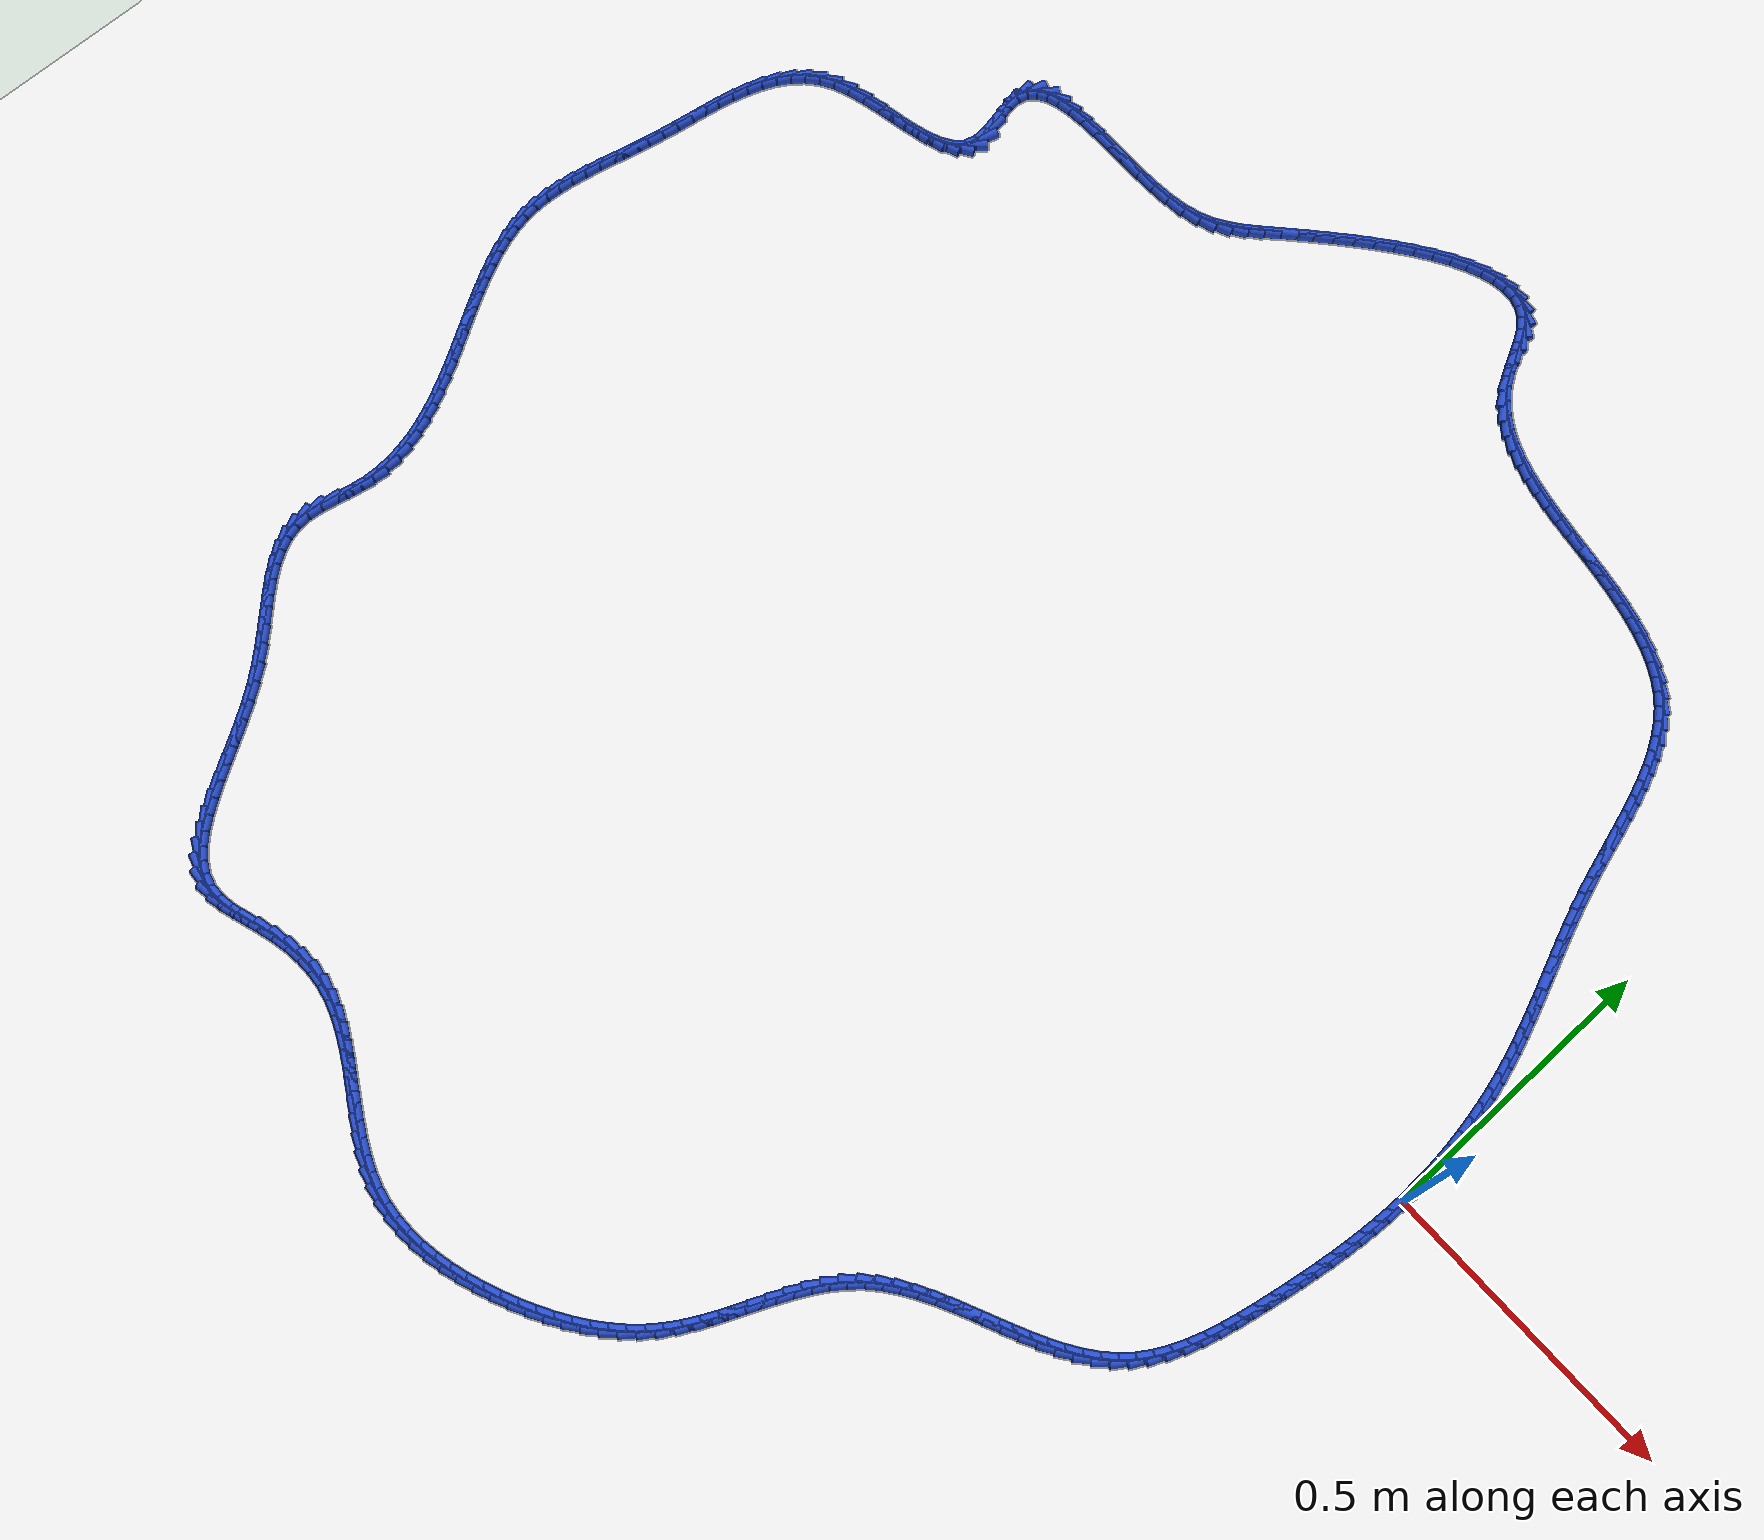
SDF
<sdf version="1.6">
 <world name="default">
  <light name="sun" type="directional">
   <pose>0 0 10 0 -0 0</pose>
   <diffuse>0.8 0.8 0.8 1</diffuse>
   <specular>0.2 0.2 0.2 1</specular>
   <attenuation>
    <range>1000</range>
    <constant>0.9</constant>
    <linear>0.01</linear>
    <quadratic>0.001</quadratic>
   </attenuation>
   <direction>-0.5 0.1 -0.9</direction>
  </light>
  <model name="ground_plane">
   <static>1</static>
   <link name="link">
    <collision name="collision">
     <geometry><plane><normal>0 0 1</normal><size>100 100</size></plane></geometry>
     <surface><friction><ode><mu>100</mu><mu2>50</mu2></ode></friction></surface>
    </collision>
    <visual name="visual">
     <cast_shadows>0</cast_shadows>
     <geometry><plane><normal>0 0 1</normal><size>100 100</size></plane></geometry>
     <material>
      <script><uri>file://media/materials/scripts/gazebo.material</uri><name>Gazebo/WhiteGlow</name></script>
     </material>
    </visual>
   </link>
  </model>
  <gravity>0 0 -9.8</gravity>
  <magnetic_field>6e-06 2.3e-05 -4.2e-05</magnetic_field>
  <atmosphere type="adiabatic"/>
  <physics name="default_physics" default="0" type="ode">
   <max_step_size>0.001</max_step_size>
   <real_time_factor>1</real_time_factor>
   <real_time_update_rate>1000</real_time_update_rate>
  </physics>
  <scene><ambient>0.4 0.4 0.4 1</ambient><background>0.7 0.7 0.7 1</background><shadows>1</shadows></scene>
  <spherical_coordinates>
   <surface_model>EARTH_WGS84</surface_model>
   <latitude_deg>0</latitude_deg>
   <longitude_deg>0</longitude_deg>
   <elevation>0</elevation>
   <heading_deg>0</heading_deg>
  </spherical_coordinates>
  <model name="line">
   <link name="link_0">
    <pose>1.0842021724855044e-17 0.0 0.01 0 1.57 -1.5688465822195459</pose>
    <collision name="collision">
     <geometry><cylinder><radius>0.01</radius><length>0.08</length></cylinder></geometry>
    </collision>
    <visual name="visual">
     <material>
      <script><name>Gazebo/Blue</name><uri>file://media/materials/scripts/gazebo.material</uri></script>
     </material>
     <geometry><cylinder><radius>0.01</radius><length>0.08</length></cylinder></geometry>
    </visual>
   </link>
   <link name="link_1">
    <pose>-5.348200174946308e-05 0.027430225812608615 0.01 0 1.57 -1.5378914910945927</pose>
    <collision name="collision">
     <geometry><cylinder><radius>0.01</radius><length>0.08</length></cylinder></geometry>
    </collision>
    <visual name="visual">
     <material>
      <script><name>Gazebo/Blue</name><uri>file://media/materials/scripts/gazebo.material</uri></script>
     </material>
     <geometry><cylinder><radius>0.01</radius><length>0.08</length></cylinder></geometry>
    </visual>
   </link>
   <link name="link_2">
    <pose>-0.0009599994611930365 0.05496995503061004 0.01 0 1.57 -1.507321143701747</pose>
    <collision name="collision">
     <geometry><cylinder><radius>0.01</radius><length>0.08</length></cylinder></geometry>
    </collision>
    <visual name="visual">
     <material>
      <script><name>Gazebo/Blue</name><uri>file://media/materials/scripts/gazebo.material</uri></script>
     </material>
     <geometry><cylinder><radius>0.01</radius><length>0.08</length></cylinder></geometry>
    </visual>
   </link>
   <link name="link_3">
    <pose>-0.0027132564170398027 0.08255398954499665 0.01 0 1.57 -1.476972287797593</pose>
    <collision name="collision">
     <geometry><cylinder><radius>0.01</radius><length>0.08</length></cylinder></geometry>
    </collision>
    <visual name="visual">
     <material>
      <script><name>Gazebo/Blue</name><uri>file://media/materials/scripts/gazebo.material</uri></script>
     </material>
     <geometry><cylinder><radius>0.01</radius><length>0.08</length></cylinder></geometry>
    </visual>
   </link>
   <link name="link_4">
    <pose>-0.005306956907998856 0.11011713124676081 0.01 0 1.57 -1.4466844124608398</pose>
    <collision name="collision">
     <geometry><cylinder><radius>0.01</radius><length>0.08</length></cylinder></geometry>
    </collision>
    <visual name="visual">
     <material>
      <script><name>Gazebo/Blue</name><uri>file://media/materials/scripts/gazebo.material</uri></script>
     </material>
     <geometry><cylinder><radius>0.01</radius><length>0.08</length></cylinder></geometry>
    </visual>
   </link>
   <link name="link_5">
    <pose>-0.008734804972779292 0.13759418202689488 0.01 0 1.57 -1.4162979856792397</pose>
    <collision name="collision">
     <geometry><cylinder><radius>0.01</radius><length>0.08</length></cylinder></geometry>
    </collision>
    <visual name="visual">
     <material>
      <script><name>Gazebo/Blue</name><uri>file://media/materials/scripts/gazebo.material</uri></script>
     </material>
     <geometry><cylinder><radius>0.01</radius><length>0.08</length></cylinder></geometry>
    </visual>
   </link>
   <link name="link_6">
    <pose>-0.012990504650090197 0.1649199437763912 0.01 0 1.57 -1.3856527033590234</pose>
    <collision name="collision">
     <geometry><cylinder><radius>0.01</radius><length>0.08</length></cylinder></geometry>
    </collision>
    <visual name="visual">
     <material>
      <script><name>Gazebo/Blue</name><uri>file://media/materials/scripts/gazebo.material</uri></script>
     </material>
     <geometry><cylinder><radius>0.01</radius><length>0.08</length></cylinder></geometry>
    </visual>
   </link>
   <link name="link_7">
    <pose>-0.018067759978640675 0.19202921838624212 0.01 0 1.57 -1.3545857551453369</pose>
    <collision name="collision">
     <geometry><cylinder><radius>0.01</radius><length>0.08</length></cylinder></geometry>
    </collision>
    <visual name="visual">
     <material>
      <script><name>Gazebo/Blue</name><uri>file://media/materials/scripts/gazebo.material</uri></script>
     </material>
     <geometry><cylinder><radius>0.01</radius><length>0.08</length></cylinder></geometry>
    </visual>
   </link>
   <link name="link_8">
    <pose>-0.023960274997139812 0.21885680774743999 0.01 0 1.57 -1.3229398415529428</pose>
    <collision name="collision">
     <geometry><cylinder><radius>0.01</radius><length>0.08</length></cylinder></geometry>
    </collision>
    <visual name="visual">
     <material>
      <script><name>Gazebo/Blue</name><uri>file://media/materials/scripts/gazebo.material</uri></script>
     </material>
     <geometry><cylinder><radius>0.01</radius><length>0.08</length></cylinder></geometry>
    </visual>
   </link>
   <link name="link_9">
    <pose>-0.03066155177834134 0.24533779857087865 0.01 0 1.57 -1.2920609871710307</pose>
    <collision name="collision">
     <geometry><cylinder><radius>0.01</radius><length>0.08</length></cylinder></geometry>
    </collision>
    <visual name="visual">
     <material>
      <script><name>Gazebo/Blue</name><uri>file://media/materials/scripts/gazebo.material</uri></script>
     </material>
     <geometry><cylinder><radius>0.01</radius><length>0.08</length></cylinder></geometry>
    </visual>
   </link>
   <link name="link_10">
    <pose>-0.03813457680169587 0.27145031179201695 0.01 0 1.57 -1.2651243190940864</pose>
    <collision name="collision">
     <geometry><cylinder><radius>0.01</radius><length>0.08</length></cylinder></geometry>
    </collision>
    <visual name="visual">
     <material>
      <script><name>Gazebo/Blue</name><uri>file://media/materials/scripts/gazebo.material</uri></script>
     </material>
     <geometry><cylinder><radius>0.01</radius><length>0.08</length></cylinder></geometry>
    </visual>
   </link>
   <link name="link_11">
    <pose>-0.046279482842719384 0.29726110697716085 0.01 0 1.57 -1.2427190493931124</pose>
    <collision name="collision">
     <geometry><cylinder><radius>0.01</radius><length>0.08</length></cylinder></geometry>
    </collision>
    <visual name="visual">
     <material>
      <script><name>Gazebo/Blue</name><uri>file://media/materials/scripts/gazebo.material</uri></script>
     </material>
     <geometry><cylinder><radius>0.01</radius><length>0.08</length></cylinder></geometry>
    </visual>
   </link>
   <link name="link_12">
    <pose>-0.05498865389918024 0.3228478713071763 0.01 0 1.57 -1.2249878372315122</pose>
    <collision name="collision">
     <geometry><cylinder><radius>0.01</radius><length>0.08</length></cylinder></geometry>
    </collision>
    <visual name="visual">
     <material>
      <script><name>Gazebo/Blue</name><uri>file://media/materials/scripts/gazebo.material</uri></script>
     </material>
     <geometry><cylinder><radius>0.01</radius><length>0.08</length></cylinder></geometry>
    </visual>
   </link>
   <link name="link_13">
    <pose>-0.06415447396884685 0.34828829196292926 0.01 0 1.57 -1.212010400052711</pose>
    <collision name="collision">
     <geometry><cylinder><radius>0.01</radius><length>0.08</length></cylinder></geometry>
    </collision>
    <visual name="visual">
     <material>
      <script><name>Gazebo/Blue</name><uri>file://media/materials/scripts/gazebo.material</uri></script>
     </material>
     <geometry><cylinder><radius>0.01</radius><length>0.08</length></cylinder></geometry>
    </visual>
   </link>
   <link name="link_14">
    <pose>-0.0736693270494876 0.37366005612528597 0.01 0 1.57 -1.2038138239094271</pose>
    <collision name="collision">
     <geometry><cylinder><radius>0.01</radius><length>0.08</length></cylinder></geometry>
    </collision>
    <visual name="visual">
     <material>
      <script><name>Gazebo/Blue</name><uri>file://media/materials/scripts/gazebo.material</uri></script>
     </material>
     <geometry><cylinder><radius>0.01</radius><length>0.08</length></cylinder></geometry>
    </visual>
   </link>
   <link name="link_15">
    <pose>-0.0834255971388709 0.3990408509751124 0.01 0 1.57 -1.2003813221050232</pose>
    <collision name="collision">
     <geometry><cylinder><radius>0.01</radius><length>0.08</length></cylinder></geometry>
    </collision>
    <visual name="visual">
     <material>
      <script><name>Gazebo/Blue</name><uri>file://media/materials/scripts/gazebo.material</uri></script>
     </material>
     <geometry><cylinder><radius>0.01</radius><length>0.08</length></cylinder></geometry>
    </visual>
   </link>
   <link name="link_16">
    <pose>-0.09331566823476516 0.4245083636932746 0.01 0 1.57 -1.2016586817462587</pose>
    <collision name="collision">
     <geometry><cylinder><radius>0.01</radius><length>0.08</length></cylinder></geometry>
    </collision>
    <visual name="visual">
     <material>
      <script><name>Gazebo/Blue</name><uri>file://media/materials/scripts/gazebo.material</uri></script>
     </material>
     <geometry><cylinder><radius>0.01</radius><length>0.08</length></cylinder></geometry>
    </visual>
   </link>
   <link name="link_17">
    <pose>-0.10323192433493875 0.4501402814606388 0.01 0 1.57 -1.2075580912577946</pose>
    <collision name="collision">
     <geometry><cylinder><radius>0.01</radius><length>0.08</length></cylinder></geometry>
    </collision>
    <visual name="visual">
     <material>
      <script><name>Gazebo/Blue</name><uri>file://media/materials/scripts/gazebo.material</uri></script>
     </material>
     <geometry><cylinder><radius>0.01</radius><length>0.08</length></cylinder></geometry>
    </visual>
   </link>
   <link name="link_18">
    <pose>-0.11306674943716007 0.47601429145807084 0.01 0 1.57 -1.2179594094985253</pose>
    <collision name="collision">
     <geometry><cylinder><radius>0.01</radius><length>0.08</length></cylinder></geometry>
    </collision>
    <visual name="visual">
     <material>
      <script><name>Gazebo/Blue</name><uri>file://media/materials/scripts/gazebo.material</uri></script>
     </material>
     <geometry><cylinder><radius>0.01</radius><length>0.08</length></cylinder></geometry>
    </visual>
   </link>
   <link name="link_19">
    <pose>-0.12271252753919752 0.5022080808664368 0.01 0 1.57 -1.2327092299663367</pose>
    <collision name="collision">
     <geometry><cylinder><radius>0.01</radius><length>0.08</length></cylinder></geometry>
    </collision>
    <visual name="visual">
     <material>
      <script><name>Gazebo/Blue</name><uri>file://media/materials/scripts/gazebo.material</uri></script>
     </material>
     <geometry><cylinder><radius>0.01</radius><length>0.08</length></cylinder></geometry>
    </visual>
   </link>
   <link name="link_20">
    <pose>-0.1320616426388195 0.528799336866603 0.01 0 1.57 -1.251618331947948</pose>
    <collision name="collision">
     <geometry><cylinder><radius>0.01</radius><length>0.08</length></cylinder></geometry>
    </collision>
    <visual name="visual">
     <material>
      <script><name>Gazebo/Blue</name><uri>file://media/materials/scripts/gazebo.material</uri></script>
     </material>
     <geometry><cylinder><radius>0.01</radius><length>0.08</length></cylinder></geometry>
    </visual>
   </link>
   <link name="link_21">
    <pose>-0.14100647873379443 0.5558657466394351 0.01 0 1.57 -1.27356786674709</pose>
    <collision name="collision">
     <geometry><cylinder><radius>0.01</radius><length>0.08</length></cylinder></geometry>
    </collision>
    <visual name="visual">
     <material>
      <script><name>Gazebo/Blue</name><uri>file://media/materials/scripts/gazebo.material</uri></script>
     </material>
     <geometry><cylinder><radius>0.01</radius><length>0.08</length></cylinder></geometry>
    </visual>
   </link>
   <link name="link_22">
    <pose>-0.14946036299888837 0.5834655715615208 0.01 0 1.57 -1.2902107235715807</pose>
    <collision name="collision">
     <geometry><cylinder><radius>0.01</radius><length>0.08</length></cylinder></geometry>
    </collision>
    <visual name="visual">
     <material>
      <script><name>Gazebo/Blue</name><uri>file://media/materials/scripts/gazebo.material</uri></script>
     </material>
     <geometry><cylinder><radius>0.01</radius><length>0.08</length></cylinder></geometry>
    </visual>
   </link>
   <link name="link_23">
    <pose>-0.1575324752259274 0.6114754102843069 0.01 0 1.57 -1.2974201162601087</pose>
    <collision name="collision">
     <geometry><cylinder><radius>0.01</radius><length>0.08</length></cylinder></geometry>
    </collision>
    <visual name="visual">
     <material>
      <script><name>Gazebo/Blue</name><uri>file://media/materials/scripts/gazebo.material</uri></script>
     </material>
     <geometry><cylinder><radius>0.01</radius><length>0.08</length></cylinder></geometry>
    </visual>
   </link>
   <link name="link_24">
    <pose>-0.16543889463695097 0.6396727070945963 0.01 0 1.57 -1.2953936369599792</pose>
    <collision name="collision">
     <geometry><cylinder><radius>0.01</radius><length>0.08</length></cylinder></geometry>
    </collision>
    <visual name="visual">
     <material>
      <script><name>Gazebo/Blue</name><uri>file://media/materials/scripts/gazebo.material</uri></script>
     </material>
     <geometry><cylinder><radius>0.01</radius><length>0.08</length></cylinder></geometry>
    </visual>
   </link>
   <link name="link_25">
    <pose>-0.17339678159336025 0.6678339034704188 0.01 0 1.57 -1.2840793312324243</pose>
    <collision name="collision">
     <geometry><cylinder><radius>0.01</radius><length>0.08</length></cylinder></geometry>
    </collision>
    <visual name="visual">
     <material>
      <script><name>Gazebo/Blue</name><uri>file://media/materials/scripts/gazebo.material</uri></script>
     </material>
     <geometry><cylinder><radius>0.01</radius><length>0.08</length></cylinder></geometry>
    </visual>
   </link>
   <link name="link_26">
    <pose>-0.18162329645655642 0.6957354408898038 0.01 0 1.57 -1.2631313429511157</pose>
    <collision name="collision">
     <geometry><cylinder><radius>0.01</radius><length>0.08</length></cylinder></geometry>
    </collision>
    <visual name="visual">
     <material>
      <script><name>Gazebo/Blue</name><uri>file://media/materials/scripts/gazebo.material</uri></script>
     </material>
     <geometry><cylinder><radius>0.01</radius><length>0.08</length></cylinder></geometry>
    </visual>
   </link>
   <link name="link_27">
    <pose>-0.19033559958794055 0.7231537608307802 0.01 0 1.57 -1.23191497111487</pose>
    <collision name="collision">
     <geometry><cylinder><radius>0.01</radius><length>0.08</length></cylinder></geometry>
    </collision>
    <visual name="visual">
     <material>
      <script><name>Gazebo/Blue</name><uri>file://media/materials/scripts/gazebo.material</uri></script>
     </material>
     <geometry><cylinder><radius>0.01</radius><length>0.08</length></cylinder></geometry>
    </visual>
   </link>
   <link name="link_28">
    <pose>-0.19975085134891385 0.7498653047713778 0.01 0 1.57 -1.1895252259751068</pose>
    <collision name="collision">
     <geometry><cylinder><radius>0.01</radius><length>0.08</length></cylinder></geometry>
    </collision>
    <visual name="visual">
     <material>
      <script><name>Gazebo/Blue</name><uri>file://media/materials/scripts/gazebo.material</uri></script>
     </material>
     <geometry><cylinder><radius>0.01</radius><length>0.08</length></cylinder></geometry>
    </visual>
   </link>
   <link name="link_29">
    <pose>-0.21008621210087747 0.7756465141896257 0.01 0 1.57 -1.1348401717042604</pose>
    <collision name="collision">
     <geometry><cylinder><radius>0.01</radius><length>0.08</length></cylinder></geometry>
    </collision>
    <visual name="visual">
     <material>
      <script><name>Gazebo/Blue</name><uri>file://media/materials/scripts/gazebo.material</uri></script>
     </material>
     <geometry><cylinder><radius>0.01</radius><length>0.08</length></cylinder></geometry>
    </visual>
   </link>
   <link name="link_30">
    <pose>-0.2215588422052326 0.8002738305635537 0.01 0 1.57 -1.0666452629942134</pose>
    <collision name="collision">
     <geometry><cylinder><radius>0.01</radius><length>0.08</length></cylinder></geometry>
    </collision>
    <visual name="visual">
     <material>
      <script><name>Gazebo/Blue</name><uri>file://media/materials/scripts/gazebo.material</uri></script>
     </material>
     <geometry><cylinder><radius>0.01</radius><length>0.08</length></cylinder></geometry>
    </visual>
   </link>
   <link name="link_31">
    <pose>-0.2343859020233804 0.8235236953711909 0.01 0 1.57 -0.9838792312952803</pose>
    <collision name="collision">
     <geometry><cylinder><radius>0.01</radius><length>0.08</length></cylinder></geometry>
    </collision>
    <visual name="visual">
     <material>
      <script><name>Gazebo/Blue</name><uri>file://media/materials/scripts/gazebo.material</uri></script>
     </material>
     <geometry><cylinder><radius>0.01</radius><length>0.08</length></cylinder></geometry>
    </visual>
   </link>
   <link name="link_32">
    <pose>-0.24878455191672197 0.8451725500905667 0.01 0 1.57 -0.8860487198223572</pose>
    <collision name="collision">
     <geometry><cylinder><radius>0.01</radius><length>0.08</length></cylinder></geometry>
    </collision>
    <visual name="visual">
     <material>
      <script><name>Gazebo/Blue</name><uri>file://media/materials/scripts/gazebo.material</uri></script>
     </material>
     <geometry><cylinder><radius>0.01</radius><length>0.08</length></cylinder></geometry>
    </visual>
   </link>
   <link name="link_33">
    <pose>-0.2649719522466585 0.8649968361997107 0.01 0 1.57 -0.7738668720317252</pose>
    <collision name="collision">
     <geometry><cylinder><radius>0.01</radius><length>0.08</length></cylinder></geometry>
    </collision>
    <visual name="visual">
     <material>
      <script><name>Gazebo/Blue</name><uri>file://media/materials/scripts/gazebo.material</uri></script>
     </material>
     <geometry><cylinder><radius>0.01</radius><length>0.08</length></cylinder></geometry>
    </visual>
   </link>
   <link name="link_34">
    <pose>-0.2831640773829902 0.8827741686550347 0.01 0 1.57 -0.6571711630845941</pose>
    <collision name="collision">
     <geometry><cylinder><radius>0.01</radius><length>0.08</length></cylinder></geometry>
    </collision>
    <visual name="visual">
     <material>
      <script><name>Gazebo/Blue</name><uri>file://media/materials/scripts/gazebo.material</uri></script>
     </material>
     <geometry><cylinder><radius>0.01</radius><length>0.08</length></cylinder></geometry>
    </visual>
   </link>
   <link name="link_35">
    <pose>-0.30343938250542674 0.8984182306588055 0.01 0 1.57 -0.5529845581469688</pose>
    <collision name="collision">
     <geometry><cylinder><radius>0.01</radius><length>0.08</length></cylinder></geometry>
    </collision>
    <visual name="visual">
     <material>
      <script><name>Gazebo/Blue</name><uri>file://media/materials/scripts/gazebo.material</uri></script>
     </material>
     <geometry><cylinder><radius>0.01</radius><length>0.08</length></cylinder></geometry>
    </visual>
   </link>
   <link name="link_36">
    <pose>-0.32561240049498186 0.9121038431076137 0.01 0 1.57 -0.4637772609129677</pose>
    <collision name="collision">
     <geometry><cylinder><radius>0.01</radius><length>0.08</length></cylinder></geometry>
    </collision>
    <visual name="visual">
     <material>
      <script><name>Gazebo/Blue</name><uri>file://media/materials/scripts/gazebo.material</uri></script>
     </material>
     <geometry><cylinder><radius>0.01</radius><length>0.08</length></cylinder></geometry>
    </visual>
   </link>
   <link name="link_37">
    <pose>-0.3494677777151367 0.9240353980874438 0.01 0 1.57 -0.3890875161422431</pose>
    <collision name="collision">
     <geometry><cylinder><radius>0.01</radius><length>0.08</length></cylinder></geometry>
    </collision>
    <visual name="visual">
     <material>
      <script><name>Gazebo/Blue</name><uri>file://media/materials/scripts/gazebo.material</uri></script>
     </material>
     <geometry><cylinder><radius>0.01</radius><length>0.08</length></cylinder></geometry>
    </visual>
   </link>
   <link name="link_38">
    <pose>-0.3747901605293725 0.9344172876842802 0.01 0 1.57 -0.3277872301772088</pose>
    <collision name="collision">
     <geometry><cylinder><radius>0.01</radius><length>0.08</length></cylinder></geometry>
    </collision>
    <visual name="visual">
     <material>
      <script><name>Gazebo/Blue</name><uri>file://media/materials/scripts/gazebo.material</uri></script>
     </material>
     <geometry><cylinder><radius>0.01</radius><length>0.08</length></cylinder></geometry>
    </visual>
   </link>
   <link name="link_39">
    <pose>-0.40136419530116996 0.9434539039841071 0.01 0 1.57 -0.27853633046413173</pose>
    <collision name="collision">
     <geometry><cylinder><radius>0.01</radius><length>0.08</length></cylinder></geometry>
    </collision>
    <visual name="visual">
     <material>
      <script><name>Gazebo/Blue</name><uri>file://media/materials/scripts/gazebo.material</uri></script>
     </material>
     <geometry><cylinder><radius>0.01</radius><length>0.08</length></cylinder></geometry>
    </visual>
   </link>
   <link name="link_40">
    <pose>-0.4289745283940098 0.9513496390729086 0.01 0 1.57 -0.24005433711603805</pose>
    <collision name="collision">
     <geometry><cylinder><radius>0.01</radius><length>0.08</length></cylinder></geometry>
    </collision>
    <visual name="visual">
     <material>
      <script><name>Gazebo/Blue</name><uri>file://media/materials/scripts/gazebo.material</uri></script>
     </material>
     <geometry><cylinder><radius>0.01</radius><length>0.08</length></cylinder></geometry>
    </visual>
   </link>
   <link name="link_41">
    <pose>-0.45740580617137333 0.9583088850366699 0.01 0 1.57 -0.21125673599701678</pose>
    <collision name="collision">
     <geometry><cylinder><radius>0.01</radius><length>0.08</length></cylinder></geometry>
    </collision>
    <visual name="visual">
     <material>
      <script><name>Gazebo/Blue</name><uri>file://media/materials/scripts/gazebo.material</uri></script>
     </material>
     <geometry><cylinder><radius>0.01</radius><length>0.08</length></cylinder></geometry>
    </visual>
   </link>
   <link name="link_42">
    <pose>-0.4864426749967415 0.9645360339613744 0.01 0 1.57 -0.19131281208131376</pose>
    <collision name="collision">
     <geometry><cylinder><radius>0.01</radius><length>0.08</length></cylinder></geometry>
    </collision>
    <visual name="visual">
     <material>
      <script><name>Gazebo/Blue</name><uri>file://media/materials/scripts/gazebo.material</uri></script>
     </material>
     <geometry><cylinder><radius>0.01</radius><length>0.08</length></cylinder></geometry>
    </visual>
   </link>
   <link name="link_43">
    <pose>-0.5158697813679042 0.9702355215677121 0.01 0 1.57 -0.18034904905734403</pose>
    <collision name="collision">
     <geometry><cylinder><radius>0.01</radius><length>0.08</length></cylinder></geometry>
    </collision>
    <visual name="visual">
     <material>
      <script><name>Gazebo/Blue</name><uri>file://media/materials/scripts/gazebo.material</uri></script>
     </material>
     <geometry><cylinder><radius>0.01</radius><length>0.08</length></cylinder></geometry>
    </visual>
   </link>
   <link name="link_44">
    <pose>-0.5454718366841503 0.9756328690216685 0.01 0 1.57 -0.1798776336098646</pose>
    <collision name="collision">
     <geometry><cylinder><radius>0.01</radius><length>0.08</length></cylinder></geometry>
    </collision>
    <visual name="visual">
     <material>
      <script><name>Gazebo/Blue</name><uri>file://media/materials/scripts/gazebo.material</uri></script>
     </material>
     <geometry><cylinder><radius>0.01</radius><length>0.08</length></cylinder></geometry>
    </visual>
   </link>
   <link name="link_45">
    <pose>-0.5750337213180423 0.9810084941661117 0.01 0 1.57 -0.19022691480345078</pose>
    <collision name="collision">
     <geometry><cylinder><radius>0.01</radius><length>0.08</length></cylinder></geometry>
    </collision>
    <visual name="visual">
     <material>
      <script><name>Gazebo/Blue</name><uri>file://media/materials/scripts/gazebo.material</uri></script>
     </material>
     <geometry><cylinder><radius>0.01</radius><length>0.08</length></cylinder></geometry>
    </visual>
   </link>
   <link name="link_46">
    <pose>-0.6043403427914732 0.9866516352214569 0.01 0 1.57 -0.21177940942751253</pose>
    <collision name="collision">
     <geometry><cylinder><radius>0.01</radius><length>0.08</length></cylinder></geometry>
    </collision>
    <visual name="visual">
     <material>
      <script><name>Gazebo/Blue</name><uri>file://media/materials/scripts/gazebo.material</uri></script>
     </material>
     <geometry><cylinder><radius>0.01</radius><length>0.08</length></cylinder></geometry>
    </visual>
   </link>
   <link name="link_47">
    <pose>-0.6331766086263358 0.9928515304081181 0.01 0 1.57 -0.24525223324633424</pose>
    <collision name="collision">
     <geometry><cylinder><radius>0.01</radius><length>0.08</length></cylinder></geometry>
    </collision>
    <visual name="visual">
     <material>
      <script><name>Gazebo/Blue</name><uri>file://media/materials/scripts/gazebo.material</uri></script>
     </material>
     <geometry><cylinder><radius>0.01</radius><length>0.08</length></cylinder></geometry>
    </visual>
   </link>
   <link name="link_48">
    <pose>-0.6613274263445226 0.9998974179465092 0.01 0 1.57 -0.29165996068379624</pose>
    <collision name="collision">
     <geometry><cylinder><radius>0.01</radius><length>0.08</length></cylinder></geometry>
    </collision>
    <visual name="visual">
     <material>
      <script><name>Gazebo/Blue</name><uri>file://media/materials/scripts/gazebo.material</uri></script>
     </material>
     <geometry><cylinder><radius>0.01</radius><length>0.08</length></cylinder></geometry>
    </visual>
   </link>
   <link name="link_49">
    <pose>-0.6885777034679268 1.0080785360570452 0.01 0 1.57 -0.3522164269146654</pose>
    <collision name="collision">
     <geometry><cylinder><radius>0.01</radius><length>0.08</length></cylinder></geometry>
    </collision>
    <visual name="visual">
     <material>
      <script><name>Gazebo/Blue</name><uri>file://media/materials/scripts/gazebo.material</uri></script>
     </material>
     <geometry><cylinder><radius>0.01</radius><length>0.08</length></cylinder></geometry>
    </visual>
   </link>
   <link name="link_50">
    <pose>-0.7147123475184414 1.0176841229601399 0.01 0 1.57 -0.4281228818178667</pose>
    <collision name="collision">
     <geometry><cylinder><radius>0.01</radius><length>0.08</length></cylinder></geometry>
    </collision>
    <visual name="visual">
     <material>
      <script><name>Gazebo/Blue</name><uri>file://media/materials/scripts/gazebo.material</uri></script>
     </material>
     <geometry><cylinder><radius>0.01</radius><length>0.08</length></cylinder></geometry>
    </visual>
   </link>
   <link name="link_51">
    <pose>-0.7395162660179588 1.0290034168762072 0.01 0 1.57 -0.5201793237297364</pose>
    <collision name="collision">
     <geometry><cylinder><radius>0.01</radius><length>0.08</length></cylinder></geometry>
    </collision>
    <visual name="visual">
     <material>
      <script><name>Gazebo/Blue</name><uri>file://media/materials/scripts/gazebo.material</uri></script>
     </material>
     <geometry><cylinder><radius>0.01</radius><length>0.08</length></cylinder></geometry>
    </visual>
   </link>
   <link name="link_52">
    <pose>-0.7627743664883726 1.0423256560256622 0.01 0 1.57 -0.628190640459535</pose>
    <collision name="collision">
     <geometry><cylinder><radius>0.01</radius><length>0.08</length></cylinder></geometry>
    </collision>
    <visual name="visual">
     <material>
      <script><name>Gazebo/Blue</name><uri>file://media/materials/scripts/gazebo.material</uri></script>
     </material>
     <geometry><cylinder><radius>0.01</radius><length>0.08</length></cylinder></geometry>
    </visual>
   </link>
   <link name="link_53">
    <pose>-0.784271556451575 1.0579400786289188 0.01 0 1.57 -0.7502735110008418</pose>
    <collision name="collision">
     <geometry><cylinder><radius>0.01</radius><length>0.08</length></cylinder></geometry>
    </collision>
    <visual name="visual">
     <material>
      <script><name>Gazebo/Blue</name><uri>file://media/materials/scripts/gazebo.material</uri></script>
     </material>
     <geometry><cylinder><radius>0.01</radius><length>0.08</length></cylinder></geometry>
    </visual>
   </link>
   <link name="link_54">
    <pose>-0.8037927434294592 1.0761359229063914 0.01 0 1.57 -0.8824037765300647</pose>
    <collision name="collision">
     <geometry><cylinder><radius>0.01</radius><length>0.08</length></cylinder></geometry>
    </collision>
    <visual name="visual">
     <material>
      <script><name>Gazebo/Blue</name><uri>file://media/materials/scripts/gazebo.material</uri></script>
     </material>
     <geometry><cylinder><radius>0.01</radius><length>0.08</length></cylinder></geometry>
    </visual>
   </link>
   <link name="link_55">
    <pose>-0.8211228349439181 1.0972024270784941 0.01 0 1.57 -1.0132176458955708</pose>
    <collision name="collision">
     <geometry><cylinder><radius>0.01</radius><length>0.08</length></cylinder></geometry>
    </collision>
    <visual name="visual">
     <material>
      <script><name>Gazebo/Blue</name><uri>file://media/materials/scripts/gazebo.material</uri></script>
     </material>
     <geometry><cylinder><radius>0.01</radius><length>0.08</length></cylinder></geometry>
    </visual>
   </link>
   <link name="link_56">
    <pose>-0.836133880896596 1.1212747318497345 0.01 0 1.57 -1.092108331354725</pose>
    <collision name="collision">
     <geometry><cylinder><radius>0.01</radius><length>0.08</length></cylinder></geometry>
    </collision>
    <visual name="visual">
     <material>
      <script><name>Gazebo/Blue</name><uri>file://media/materials/scripts/gazebo.material</uri></script>
     </material>
     <geometry><cylinder><radius>0.01</radius><length>0.08</length></cylinder></geometry>
    </visual>
   </link>
   <link name="link_57">
    <pose>-0.8495104327564988 1.1470511974102653 0.01 0 1.57 -1.101785781525811</pose>
    <collision name="collision">
     <geometry><cylinder><radius>0.01</radius><length>0.08</length></cylinder></geometry>
    </collision>
    <visual name="visual">
     <material>
      <script><name>Gazebo/Blue</name><uri>file://media/materials/scripts/gazebo.material</uri></script>
     </material>
     <geometry><cylinder><radius>0.01</radius><length>0.08</length></cylinder></geometry>
    </visual>
   </link>
   <link name="link_58">
    <pose>-0.8623794615742008 1.1724478348945604 0.01 0 1.57 -1.038824736902109</pose>
    <collision name="collision">
     <geometry><cylinder><radius>0.01</radius><length>0.08</length></cylinder></geometry>
    </collision>
    <visual name="visual">
     <material>
      <script><name>Gazebo/Blue</name><uri>file://media/materials/scripts/gazebo.material</uri></script>
     </material>
     <geometry><cylinder><radius>0.01</radius><length>0.08</length></cylinder></geometry>
    </visual>
   </link>
   <link name="link_59">
    <pose>-0.8758723774967677 1.195372805597045 0.01 0 1.57 -0.8782950866586984</pose>
    <collision name="collision">
     <geometry><cylinder><radius>0.01</radius><length>0.08</length></cylinder></geometry>
    </collision>
    <visual name="visual">
     <material>
      <script><name>Gazebo/Blue</name><uri>file://media/materials/scripts/gazebo.material</uri></script>
     </material>
     <geometry><cylinder><radius>0.01</radius><length>0.08</length></cylinder></geometry>
    </visual>
   </link>
   <link name="link_60">
    <pose>-0.8911140504372053 1.2137462318572307 0.01 0 1.57 -0.6219325225921754</pose>
    <collision name="collision">
     <geometry><cylinder><radius>0.01</radius><length>0.08</length></cylinder></geometry>
    </collision>
    <visual name="visual">
     <material>
      <script><name>Gazebo/Blue</name><uri>file://media/materials/scripts/gazebo.material</uri></script>
     </material>
     <geometry><cylinder><radius>0.01</radius><length>0.08</length></cylinder></geometry>
    </visual>
   </link>
   <link name="link_61">
    <pose>-0.9087408365223874 1.226381649823152 0.01 0 1.57 -0.3486219513642271</pose>
    <collision name="collision">
     <geometry><cylinder><radius>0.01</radius><length>0.08</length></cylinder></geometry>
    </collision>
    <visual name="visual">
     <material>
      <script><name>Gazebo/Blue</name><uri>file://media/materials/scripts/gazebo.material</uri></script>
     </material>
     <geometry><cylinder><radius>0.01</radius><length>0.08</length></cylinder></geometry>
    </visual>
   </link>
   <link name="link_62">
    <pose>-0.9285707642904768 1.2335891862988424 0.01 0 1.57 -0.1021796450608524</pose>
    <collision name="collision">
     <geometry><cylinder><radius>0.01</radius><length>0.08</length></cylinder></geometry>
    </collision>
    <visual name="visual">
     <material>
      <script><name>Gazebo/Blue</name><uri>file://media/materials/scripts/gazebo.material</uri></script>
     </material>
     <geometry><cylinder><radius>0.01</radius><length>0.08</length></cylinder></geometry>
    </visual>
   </link>
   <link name="link_63">
    <pose>-0.9503438046825492 1.235821722985079 0.01 0 1.57 0.09730299091059869</pose>
    <collision name="collision">
     <geometry><cylinder><radius>0.01</radius><length>0.08</length></cylinder></geometry>
    </collision>
    <visual name="visual">
     <material>
      <script><name>Gazebo/Blue</name><uri>file://media/materials/scripts/gazebo.material</uri></script>
     </material>
     <geometry><cylinder><radius>0.01</radius><length>0.08</length></cylinder></geometry>
    </visual>
   </link>
   <link name="link_64">
    <pose>-0.9737999286396805 1.2335321415826392 0.01 0 1.57 0.25023093979470123</pose>
    <collision name="collision">
     <geometry><cylinder><radius>0.01</radius><length>0.08</length></cylinder></geometry>
    </collision>
    <visual name="visual">
     <material>
      <script><name>Gazebo/Blue</name><uri>file://media/materials/scripts/gazebo.material</uri></script>
     </material>
     <geometry><cylinder><radius>0.01</radius><length>0.08</length></cylinder></geometry>
    </visual>
   </link>
   <link name="link_65">
    <pose>-0.9986791071029464 1.2271733237923006 0.01 0 1.57 0.3657996234086984</pose>
    <collision name="collision">
     <geometry><cylinder><radius>0.01</radius><length>0.08</length></cylinder></geometry>
    </collision>
    <visual name="visual">
     <material>
      <script><name>Gazebo/Blue</name><uri>file://media/materials/scripts/gazebo.material</uri></script>
     </material>
     <geometry><cylinder><radius>0.01</radius><length>0.08</length></cylinder></geometry>
    </visual>
   </link>
   <link name="link_66">
    <pose>-1.024721311013423 1.2171981513148395 0.01 0 1.57 0.45368346202330473</pose>
    <collision name="collision">
     <geometry><cylinder><radius>0.01</radius><length>0.08</length></cylinder></geometry>
    </collision>
    <visual name="visual">
     <material>
      <script><name>Gazebo/Blue</name><uri>file://media/materials/scripts/gazebo.material</uri></script>
     </material>
     <geometry><cylinder><radius>0.01</radius><length>0.08</length></cylinder></geometry>
    </visual>
   </link>
   <link name="link_67">
    <pose>-1.0516665113121868 1.2040595058510333 0.01 0 1.57 0.5214539235836061</pose>
    <collision name="collision">
     <geometry><cylinder><radius>0.01</radius><length>0.08</length></cylinder></geometry>
    </collision>
    <visual name="visual">
     <material>
      <script><name>Gazebo/Blue</name><uri>file://media/materials/scripts/gazebo.material</uri></script>
     </material>
     <geometry><cylinder><radius>0.01</radius><length>0.08</length></cylinder></geometry>
    </visual>
   </link>
   <link name="link_68">
    <pose>-1.079254678940313 1.1882102691016596 0.01 0 1.57 0.5745062912305148</pose>
    <collision name="collision">
     <geometry><cylinder><radius>0.01</radius><length>0.08</length></cylinder></geometry>
    </collision>
    <visual name="visual">
     <material>
      <script><name>Gazebo/Blue</name><uri>file://media/materials/scripts/gazebo.material</uri></script>
     </material>
     <geometry><cylinder><radius>0.01</radius><length>0.08</length></cylinder></geometry>
    </visual>
   </link>
   <link name="link_69">
    <pose>-1.1072257848388778 1.1701033227674955 0.01 0 1.57 0.6165776804479559</pose>
    <collision name="collision">
     <geometry><cylinder><radius>0.01</radius><length>0.08</length></cylinder></geometry>
    </collision>
    <visual name="visual">
     <material>
      <script><name>Gazebo/Blue</name><uri>file://media/materials/scripts/gazebo.material</uri></script>
     </material>
     <geometry><cylinder><radius>0.01</radius><length>0.08</length></cylinder></geometry>
    </visual>
   </link>
   <link name="link_70">
    <pose>-1.1353197999489573 1.150191548549317 0.01 0 1.57 0.6502439988474986</pose>
    <collision name="collision">
     <geometry><cylinder><radius>0.01</radius><length>0.08</length></cylinder></geometry>
    </collision>
    <visual name="visual">
     <material>
      <script><name>Gazebo/Blue</name><uri>file://media/materials/scripts/gazebo.material</uri></script>
     </material>
     <geometry><cylinder><radius>0.01</radius><length>0.08</length></cylinder></geometry>
    </visual>
   </link>
   <link name="link_71">
    <pose>-1.1632766952116276 1.1289278281479032 0.01 0 1.57 0.6772798606839608</pose>
    <collision name="collision">
     <geometry><cylinder><radius>0.01</radius><length>0.08</length></cylinder></geometry>
    </collision>
    <visual name="visual">
     <material>
      <script><name>Gazebo/Blue</name><uri>file://media/materials/scripts/gazebo.material</uri></script>
     </material>
     <geometry><cylinder><radius>0.01</radius><length>0.08</length></cylinder></geometry>
    </visual>
   </link>
   <link name="link_72">
    <pose>-1.1908364415679642 1.1067650432640304 0.01 0 1.57 0.6988953716993768</pose>
    <collision name="collision">
     <geometry><cylinder><radius>0.01</radius><length>0.08</length></cylinder></geometry>
    </collision>
    <visual name="visual">
     <material>
      <script><name>Gazebo/Blue</name><uri>file://media/materials/scripts/gazebo.material</uri></script>
     </material>
     <geometry><cylinder><radius>0.01</radius><length>0.08</length></cylinder></geometry>
    </visual>
   </link>
   <link name="link_73">
    <pose>-1.217739009959043 1.0841560755984754 0.01 0 1.57 0.7158816792470567</pose>
    <collision name="collision">
     <geometry><cylinder><radius>0.01</radius><length>0.08</length></cylinder></geometry>
    </collision>
    <visual name="visual">
     <material>
      <script><name>Gazebo/Blue</name><uri>file://media/materials/scripts/gazebo.material</uri></script>
     </material>
     <geometry><cylinder><radius>0.01</radius><length>0.08</length></cylinder></geometry>
    </visual>
   </link>
   <link name="link_74">
    <pose>-1.2437243713259403 1.0615538068520156 0.01 0 1.57 0.7286881943029709</pose>
    <collision name="collision">
     <geometry><cylinder><radius>0.01</radius><length>0.08</length></cylinder></geometry>
    </collision>
    <visual name="visual">
     <material>
      <script><name>Gazebo/Blue</name><uri>file://media/materials/scripts/gazebo.material</uri></script>
     </material>
     <geometry><cylinder><radius>0.01</radius><length>0.08</length></cylinder></geometry>
    </visual>
   </link>
   <link name="link_75">
    <pose>-1.2685324966097327 1.039411118725428 0.01 0 1.57 0.7374391783126011</pose>
    <collision name="collision">
     <geometry><cylinder><radius>0.01</radius><length>0.08</length></cylinder></geometry>
    </collision>
    <visual name="visual">
     <material>
      <script><name>Gazebo/Blue</name><uri>file://media/materials/scripts/gazebo.material</uri></script>
     </material>
     <geometry><cylinder><radius>0.01</radius><length>0.08</length></cylinder></geometry>
    </visual>
   </link>
   <link name="link_76">
    <pose>-1.291903389928156 1.018180891363287 0.01 0 1.57 0.7365936619908413</pose>
    <collision name="collision">
     <geometry><cylinder><radius>0.01</radius><length>0.08</length></cylinder></geometry>
    </collision>
    <visual name="visual">
     <material>
      <script><name>Gazebo/Blue</name><uri>file://media/materials/scripts/gazebo.material</uri></script>
     </material>
     <geometry><cylinder><radius>0.01</radius><length>0.08</length></cylinder></geometry>
    </visual>
   </link>
   <link name="link_77">
    <pose>-1.3138210802229968 0.9983045585415887 0.01 0 1.57 0.7053982513814845</pose>
    <collision name="collision">
     <geometry><cylinder><radius>0.01</radius><length>0.08</length></cylinder></geometry>
    </collision>
    <visual name="visual">
     <material>
      <script><name>Gazebo/Blue</name><uri>file://media/materials/scripts/gazebo.material</uri></script>
     </material>
     <geometry><cylinder><radius>0.01</radius><length>0.08</length></cylinder></geometry>
    </visual>
   </link>
   <link name="link_78">
    <pose>-1.3350996364459973 0.980184619702808 0.01 0 1.57 0.6359717099641948</pose>
    <collision name="collision">
     <geometry><cylinder><radius>0.01</radius><length>0.08</length></cylinder></geometry>
    </collision>
    <visual name="visual">
     <material>
      <script><name>Gazebo/Blue</name><uri>file://media/materials/scripts/gazebo.material</uri></script>
     </material>
     <geometry><cylinder><radius>0.01</radius><length>0.08</length></cylinder></geometry>
    </visual>
   </link>
   <link name="link_79">
    <pose>-1.3567294495932747 0.9642153036263181 0.01 0 1.57 0.5288680740715266</pose>
    <collision name="collision">
     <geometry><cylinder><radius>0.01</radius><length>0.08</length></cylinder></geometry>
    </collision>
    <visual name="visual">
     <material>
      <script><name>Gazebo/Blue</name><uri>file://media/materials/scripts/gazebo.material</uri></script>
     </material>
     <geometry><cylinder><radius>0.01</radius><length>0.08</length></cylinder></geometry>
    </visual>
   </link>
   <link name="link_80">
    <pose>-1.3797009106609477 0.950790839091492 0.01 0 1.57 0.3928451804721419</pose>
    <collision name="collision">
     <geometry><cylinder><radius>0.01</radius><length>0.08</length></cylinder></geometry>
    </collision>
    <visual name="visual">
     <material>
      <script><name>Gazebo/Blue</name><uri>file://media/materials/scripts/gazebo.material</uri></script>
     </material>
     <geometry><cylinder><radius>0.01</radius><length>0.08</length></cylinder></geometry>
    </visual>
   </link>
   <link name="link_81">
    <pose>-1.4050044106451343 0.9403054548777025 0.01 0 1.57 0.24761680611885878</pose>
    <collision name="collision">
     <geometry><cylinder><radius>0.01</radius><length>0.08</length></cylinder></geometry>
    </collision>
    <visual name="visual">
     <material>
      <script><name>Gazebo/Blue</name><uri>file://media/materials/scripts/gazebo.material</uri></script>
     </material>
     <geometry><cylinder><radius>0.01</radius><length>0.08</length></cylinder></geometry>
    </visual>
   </link>
   <link name="link_82">
    <pose>-1.4335293691621445 0.933094206067047 0.01 0 1.57 0.13297187077041794</pose>
    <collision name="collision">
     <geometry><cylinder><radius>0.01</radius><length>0.08</length></cylinder></geometry>
    </collision>
    <visual name="visual">
     <material>
      <script><name>Gazebo/Blue</name><uri>file://media/materials/scripts/gazebo.material</uri></script>
     </material>
     <geometry><cylinder><radius>0.01</radius><length>0.08</length></cylinder></geometry>
    </visual>
   </link>
   <link name="link_83">
    <pose>-1.4651047118466998 0.928870651333952 0.01 0 1.57 0.05593800054021079</pose>
    <collision name="collision">
     <geometry><cylinder><radius>0.01</radius><length>0.08</length></cylinder></geometry>
    </collision>
    <visual name="visual">
     <material>
      <script><name>Gazebo/Blue</name><uri>file://media/materials/scripts/gazebo.material</uri></script>
     </material>
     <geometry><cylinder><radius>0.01</radius><length>0.08</length></cylinder></geometry>
    </visual>
   </link>
   <link name="link_84">
    <pose>-1.4989253933702482 0.9269768143106053 0.01 0 1.57 0.006441747097596129</pose>
    <collision name="collision">
     <geometry><cylinder><radius>0.01</radius><length>0.08</length></cylinder></geometry>
    </collision>
    <visual name="visual">
     <material>
      <script><name>Gazebo/Blue</name><uri>file://media/materials/scripts/gazebo.material</uri></script>
     </material>
     <geometry><cylinder><radius>0.01</radius><length>0.08</length></cylinder></geometry>
    </visual>
   </link>
   <link name="link_85">
    <pose>-1.5341778454294006 0.9267497237887373 0.01 0 1.57 -0.02164898980343656</pose>
    <collision name="collision">
     <geometry><cylinder><radius>0.01</radius><length>0.08</length></cylinder></geometry>
    </collision>
    <visual name="visual">
     <material>
      <script><name>Gazebo/Blue</name><uri>file://media/materials/scripts/gazebo.material</uri></script>
     </material>
     <geometry><cylinder><radius>0.01</radius><length>0.08</length></cylinder></geometry>
    </visual>
   </link>
   <link name="link_86">
    <pose>-1.5700484997207664 0.9275264085600768 0.01 0 1.57 -0.03131365263800175</pose>
    <collision name="collision">
     <geometry><cylinder><radius>0.01</radius><length>0.08</length></cylinder></geometry>
    </collision>
    <visual name="visual">
     <material>
      <script><name>Gazebo/Blue</name><uri>file://media/materials/scripts/gazebo.material</uri></script>
     </material>
     <geometry><cylinder><radius>0.01</radius><length>0.08</length></cylinder></geometry>
    </visual>
   </link>
   <link name="link_87">
    <pose>-1.6057237879409538 0.928643897416354 0.01 0 1.57 -0.02293815620261843</pose>
    <collision name="collision">
     <geometry><cylinder><radius>0.01</radius><length>0.08</length></cylinder></geometry>
    </collision>
    <visual name="visual">
     <material>
      <script><name>Gazebo/Blue</name><uri>file://media/materials/scripts/gazebo.material</uri></script>
     </material>
     <geometry><cylinder><radius>0.01</radius><length>0.08</length></cylinder></geometry>
    </visual>
   </link>
   <link name="link_88">
    <pose>-1.6403901417865732 0.9294392191492984 0.01 0 1.57 0.00577930049596079</pose>
    <collision name="collision">
     <geometry><cylinder><radius>0.01</radius><length>0.08</length></cylinder></geometry>
    </collision>
    <visual name="visual">
     <material>
      <script><name>Gazebo/Blue</name><uri>file://media/materials/scripts/gazebo.material</uri></script>
     </material>
     <geometry><cylinder><radius>0.01</radius><length>0.08</length></cylinder></geometry>
    </visual>
   </link>
   <link name="link_89">
    <pose>-1.673233992954234 0.9292494025506398 0.01 0 1.57 0.06076789634919975</pose>
    <collision name="collision">
     <geometry><cylinder><radius>0.01</radius><length>0.08</length></cylinder></geometry>
    </collision>
    <visual name="visual">
     <material>
      <script><name>Gazebo/Blue</name><uri>file://media/materials/scripts/gazebo.material</uri></script>
     </material>
     <geometry><cylinder><radius>0.01</radius><length>0.08</length></cylinder></geometry>
    </visual>
   </link>
   <link name="link_90">
    <pose>-1.7034417731405451 0.9274114764121071 0.01 0 1.57 0.1538308614129684</pose>
    <collision name="collision">
     <geometry><cylinder><radius>0.01</radius><length>0.08</length></cylinder></geometry>
    </collision>
    <visual name="visual">
     <material>
      <script><name>Gazebo/Blue</name><uri>file://media/materials/scripts/gazebo.material</uri></script>
     </material>
     <geometry><cylinder><radius>0.01</radius><length>0.08</length></cylinder></geometry>
    </visual>
   </link>
   <link name="link_91">
    <pose>-1.7301999140421167 0.9232624695254306 0.01 0 1.57 0.3066627154247082</pose>
    <collision name="collision">
     <geometry><cylinder><radius>0.01</radius><length>0.08</length></cylinder></geometry>
    </collision>
    <visual name="visual">
     <material>
      <script><name>Gazebo/Blue</name><uri>file://media/materials/scripts/gazebo.material</uri></script>
     </material>
     <geometry><cylinder><radius>0.01</radius><length>0.08</length></cylinder></geometry>
    </visual>
   </link>
   <link name="link_92">
    <pose>-1.752694847355558 0.9161394106823397 0.01 0 1.57 0.553369470734675</pose>
    <collision name="collision">
     <geometry><cylinder><radius>0.01</radius><length>0.08</length></cylinder></geometry>
    </collision>
    <visual name="visual">
     <material>
      <script><name>Gazebo/Blue</name><uri>file://media/materials/scripts/gazebo.material</uri></script>
     </material>
     <geometry><cylinder><radius>0.01</radius><length>0.08</length></cylinder></geometry>
    </visual>
   </link>
   <link name="link_93">
    <pose>-1.7701130047774774 0.9053793286745638 0.01 0 1.57 0.9174770669892862</pose>
    <collision name="collision">
     <geometry><cylinder><radius>0.01</radius><length>0.08</length></cylinder></geometry>
    </collision>
    <visual name="visual">
     <material>
      <script><name>Gazebo/Blue</name><uri>file://media/materials/scripts/gazebo.material</uri></script>
     </material>
     <geometry><cylinder><radius>0.01</radius><length>0.08</length></cylinder></geometry>
    </visual>
   </link>
   <link name="link_94">
    <pose>-1.781640818004486 0.890319252293833 0.01 0 1.57 1.334384019429499</pose>
    <collision name="collision">
     <geometry><cylinder><radius>0.01</radius><length>0.08</length></cylinder></geometry>
    </collision>
    <visual name="visual">
     <material>
      <script><name>Gazebo/Blue</name><uri>file://media/materials/scripts/gazebo.material</uri></script>
     </material>
     <geometry><cylinder><radius>0.01</radius><length>0.08</length></cylinder></geometry>
    </visual>
   </link>
   <link name="link_95">
    <pose>-1.7864647187331921 0.8702962103318765 0.01 0 1.57 -1.486660065563127</pose>
    <collision name="collision">
     <geometry><cylinder><radius>0.01</radius><length>0.08</length></cylinder></geometry>
    </collision>
    <visual name="visual">
     <material>
      <script><name>Gazebo/Blue</name><uri>file://media/materials/scripts/gazebo.material</uri></script>
     </material>
     <geometry><cylinder><radius>0.01</radius><length>0.08</length></cylinder></geometry>
    </visual>
   </link>
   <link name="link_96">
    <pose>-1.784335300283696 0.8450467947844211 0.01 0 1.57 -1.3608108798278207</pose>
    <collision name="collision">
     <geometry><cylinder><radius>0.01</radius><length>0.08</length></cylinder></geometry>
    </collision>
    <visual name="visual">
     <material>
      <script><name>Gazebo/Blue</name><uri>file://media/materials/scripts/gazebo.material</uri></script>
     </material>
     <geometry><cylinder><radius>0.01</radius><length>0.08</length></cylinder></geometry>
    </visual>
   </link>
   <link name="link_97">
    <pose>-1.7782783110785003 0.816627201483778 0.01 0 1.57 -1.372055091858556</pose>
    <collision name="collision">
     <geometry><cylinder><radius>0.01</radius><length>0.08</length></cylinder></geometry>
    </collision>
    <visual name="visual">
     <material>
      <script><name>Gazebo/Blue</name><uri>file://media/materials/scripts/gazebo.material</uri></script>
     </material>
     <geometry><cylinder><radius>0.01</radius><length>0.08</length></cylinder></geometry>
    </visual>
   </link>
   <link name="link_98">
    <pose>-1.7724984126844796 0.7879285825825513 0.01 0 1.57 -1.5211317537154543</pose>
    <collision name="collision">
     <geometry><cylinder><radius>0.01</radius><length>0.08</length></cylinder></geometry>
    </collision>
    <visual name="visual">
     <material>
      <script><name>Gazebo/Blue</name><uri>file://media/materials/scripts/gazebo.material</uri></script>
     </material>
     <geometry><cylinder><radius>0.01</radius><length>0.08</length></cylinder></geometry>
    </visual>
   </link>
   <link name="link_99">
    <pose>-1.7712018268420573 0.7618431952144615 0.01 0 1.57 1.2691365704809239</pose>
    <collision name="collision">
     <geometry><cylinder><radius>0.01</radius><length>0.08</length></cylinder></geometry>
    </collision>
    <visual name="visual">
     <material>
      <script><name>Gazebo/Blue</name><uri>file://media/materials/scripts/gazebo.material</uri></script>
     </material>
     <geometry><cylinder><radius>0.01</radius><length>0.08</length></cylinder></geometry>
    </visual>
   </link>
   <link name="link_100">
    <pose>-1.7777800754076347 0.740701859048506 0.01 0 1.57 0.857307606666855</pose>
    <collision name="collision">
     <geometry><cylinder><radius>0.01</radius><length>0.08</length></cylinder></geometry>
    </collision>
    <visual name="visual">
     <material>
      <script><name>Gazebo/Blue</name><uri>file://media/materials/scripts/gazebo.material</uri></script>
     </material>
     <geometry><cylinder><radius>0.01</radius><length>0.08</length></cylinder></geometry>
    </visual>
   </link>
   <link name="link_101">
    <pose>-1.7919657230880293 0.7243138816411913 0.01 0 1.57 0.5487560092563504</pose>
    <collision name="collision">
     <geometry><cylinder><radius>0.01</radius><length>0.08</length></cylinder></geometry>
    </collision>
    <visual name="visual">
     <material>
      <script><name>Gazebo/Blue</name><uri>file://media/materials/scripts/gazebo.material</uri></script>
     </material>
     <geometry><cylinder><radius>0.01</radius><length>0.08</length></cylinder></geometry>
    </visual>
   </link>
   <link name="link_102">
    <pose>-1.8124645691250199 0.7117809914627069 0.01 0 1.57 0.3590090551290451</pose>
    <collision name="collision">
     <geometry><cylinder><radius>0.01</radius><length>0.08</length></cylinder></geometry>
    </collision>
    <visual name="visual">
     <material>
      <script><name>Gazebo/Blue</name><uri>file://media/materials/scripts/gazebo.material</uri></script>
     </material>
     <geometry><cylinder><radius>0.01</radius><length>0.08</length></cylinder></geometry>
    </visual>
   </link>
   <link name="link_103">
    <pose>-1.8379823601459107 0.7022048807248142 0.01 0 1.57 0.25163042361700283</pose>
    <collision name="collision">
     <geometry><cylinder><radius>0.01</radius><length>0.08</length></cylinder></geometry>
    </collision>
    <visual name="visual">
     <material>
      <script><name>Gazebo/Blue</name><uri>file://media/materials/scripts/gazebo.material</uri></script>
     </material>
     <geometry><cylinder><radius>0.01</radius><length>0.08</length></cylinder></geometry>
    </visual>
   </link>
   <link name="link_104">
    <pose>-1.867224842778005 0.6946872416392738 0.01 0 1.57 0.19809039820069696</pose>
    <collision name="collision">
     <geometry><cylinder><radius>0.01</radius><length>0.08</length></cylinder></geometry>
    </collision>
    <visual name="visual">
     <material>
      <script><name>Gazebo/Blue</name><uri>file://media/materials/scripts/gazebo.material</uri></script>
     </material>
     <geometry><cylinder><radius>0.01</radius><length>0.08</length></cylinder></geometry>
    </visual>
   </link>
   <link name="link_105">
    <pose>-1.898897763648607 0.6883297664178465 0.01 0 1.57 0.18369596860150592</pose>
    <collision name="collision">
     <geometry><cylinder><radius>0.01</radius><length>0.08</length></cylinder></geometry>
    </collision>
    <visual name="visual">
     <material>
      <script><name>Gazebo/Blue</name><uri>file://media/materials/scripts/gazebo.material</uri></script>
     </material>
     <geometry><cylinder><radius>0.01</radius><length>0.08</length></cylinder></geometry>
    </visual>
   </link>
   <link name="link_106">
    <pose>-1.9317068693850201 0.6822341472722931 0.01 0 1.57 0.20333309432680033</pose>
    <collision name="collision">
     <geometry><cylinder><radius>0.01</radius><length>0.08</length></cylinder></geometry>
    </collision>
    <visual name="visual">
     <material>
      <script><name>Gazebo/Blue</name><uri>file://media/materials/scripts/gazebo.material</uri></script>
     </material>
     <geometry><cylinder><radius>0.01</radius><length>0.08</length></cylinder></geometry>
    </visual>
   </link>
   <link name="link_107">
    <pose>-1.9643579066145487 0.6755020764143749 0.01 0 1.57 0.2590208960032586</pose>
    <collision name="collision">
     <geometry><cylinder><radius>0.01</radius><length>0.08</length></cylinder></geometry>
    </collision>
    <visual name="visual">
     <material>
      <script><name>Gazebo/Blue</name><uri>file://media/materials/scripts/gazebo.material</uri></script>
     </material>
     <geometry><cylinder><radius>0.01</radius><length>0.08</length></cylinder></geometry>
    </visual>
   </link>
   <link name="link_108">
    <pose>-1.9955566219644962 0.6672352460558525 0.01 0 1.57 0.35970538378309513</pose>
    <collision name="collision">
     <geometry><cylinder><radius>0.01</radius><length>0.08</length></cylinder></geometry>
    </collision>
    <visual name="visual">
     <material>
      <script><name>Gazebo/Blue</name><uri>file://media/materials/scripts/gazebo.material</uri></script>
     </material>
     <geometry><cylinder><radius>0.01</radius><length>0.08</length></cylinder></geometry>
    </visual>
   </link>
   <link name="link_109">
    <pose>-2.024008762062166 0.6565353484084868 0.01 0 1.57 0.516553195965366</pose>
    <collision name="collision">
     <geometry><cylinder><radius>0.01</radius><length>0.08</length></cylinder></geometry>
    </collision>
    <visual name="visual">
     <material>
      <script><name>Gazebo/Blue</name><uri>file://media/materials/scripts/gazebo.material</uri></script>
     </material>
     <geometry><cylinder><radius>0.01</radius><length>0.08</length></cylinder></geometry>
    </visual>
   </link>
   <link name="link_110">
    <pose>-2.0485483530769217 0.6425970063042622 0.01 0 1.57 0.6973352669385511</pose>
    <collision name="collision">
     <geometry><cylinder><radius>0.01</radius><length>0.08</length></cylinder></geometry>
    </collision>
    <visual name="visual">
     <material>
      <script><name>Gazebo/Blue</name><uri>file://media/materials/scripts/gazebo.material</uri></script>
     </material>
     <geometry><cylinder><radius>0.01</radius><length>0.08</length></cylinder></geometry>
    </visual>
   </link>
   <link name="link_111">
    <pose>-2.069084061514904 0.6253933532512365 0.01 0 1.57 0.8696262016092936</pose>
    <collision name="collision">
     <geometry><cylinder><radius>0.01</radius><length>0.08</length></cylinder></geometry>
    </collision>
    <visual name="visual">
     <material>
      <script><name>Gazebo/Blue</name><uri>file://media/materials/scripts/gazebo.material</uri></script>
     </material>
     <geometry><cylinder><radius>0.01</radius><length>0.08</length></cylinder></geometry>
    </visual>
   </link>
   <link name="link_112">
    <pose>-2.086060620894317 0.6052858702609963 0.01 0 1.57 1.0214029645124276</pose>
    <collision name="collision">
     <geometry><cylinder><radius>0.01</radius><length>0.08</length></cylinder></geometry>
    </collision>
    <visual name="visual">
     <material>
      <script><name>Gazebo/Blue</name><uri>file://media/materials/scripts/gazebo.material</uri></script>
     </material>
     <geometry><cylinder><radius>0.01</radius><length>0.08</length></cylinder></geometry>
    </visual>
   </link>
   <link name="link_113">
    <pose>-2.099926705042605 0.5826388928562675 0.01 0 1.57 1.1467931466080155</pose>
    <collision name="collision">
     <geometry><cylinder><radius>0.01</radius><length>0.08</length></cylinder></geometry>
    </collision>
    <visual name="visual">
     <material>
      <script><name>Gazebo/Blue</name><uri>file://media/materials/scripts/gazebo.material</uri></script>
     </material>
     <geometry><cylinder><radius>0.01</radius><length>0.08</length></cylinder></geometry>
    </visual>
   </link>
   <link name="link_114">
    <pose>-2.111130987787217 0.5578167565597769 0.01 0 1.57 1.2452151497944808</pose>
    <collision name="collision">
     <geometry><cylinder><radius>0.01</radius><length>0.08</length></cylinder></geometry>
    </collision>
    <visual name="visual">
     <material>
      <script><name>Gazebo/Blue</name><uri>file://media/materials/scripts/gazebo.material</uri></script>
     </material>
     <geometry><cylinder><radius>0.01</radius><length>0.08</length></cylinder></geometry>
    </visual>
   </link>
   <link name="link_115">
    <pose>-2.1201221429555974 0.5311837968942501 0.01 0 1.57 1.318896851618534</pose>
    <collision name="collision">
     <geometry><cylinder><radius>0.01</radius><length>0.08</length></cylinder></geometry>
    </collision>
    <visual name="visual">
     <material>
      <script><name>Gazebo/Blue</name><uri>file://media/materials/scripts/gazebo.material</uri></script>
     </material>
     <geometry><cylinder><radius>0.01</radius><length>0.08</length></cylinder></geometry>
    </visual>
   </link>
   <link name="link_116">
    <pose>-2.127348844375191 0.5031043493824141 0.01 0 1.57 1.3708104059334882</pose>
    <collision name="collision">
     <geometry><cylinder><radius>0.01</radius><length>0.08</length></cylinder></geometry>
    </collision>
    <visual name="visual">
     <material>
      <script><name>Gazebo/Blue</name><uri>file://media/materials/scripts/gazebo.material</uri></script>
     </material>
     <geometry><cylinder><radius>0.01</radius><length>0.08</length></cylinder></geometry>
    </visual>
   </link>
   <link name="link_117">
    <pose>-2.1332597658734453 0.47394274954699506 0.01 0 1.57 1.4035671666285718</pose>
    <collision name="collision">
     <geometry><cylinder><radius>0.01</radius><length>0.08</length></cylinder></geometry>
    </collision>
    <visual name="visual">
     <material>
      <script><name>Gazebo/Blue</name><uri>file://media/materials/scripts/gazebo.material</uri></script>
     </material>
     <geometry><cylinder><radius>0.01</radius><length>0.08</length></cylinder></geometry>
    </visual>
   </link>
   <link name="link_118">
    <pose>-2.138303581277806 0.4440633329107185 0.01 0 1.57 1.4189817807922733</pose>
    <collision name="collision">
     <geometry><cylinder><radius>0.01</radius><length>0.08</length></cylinder></geometry>
    </collision>
    <visual name="visual">
     <material>
      <script><name>Gazebo/Blue</name><uri>file://media/materials/scripts/gazebo.material</uri></script>
     </material>
     <geometry><cylinder><radius>0.01</radius><length>0.08</length></cylinder></geometry>
    </visual>
   </link>
   <link name="link_119">
    <pose>-2.142928964415718 0.41383043499631167 0.01 0 1.57 1.417950493739882</pose>
    <collision name="collision">
     <geometry><cylinder><radius>0.01</radius><length>0.08</length></cylinder></geometry>
    </collision>
    <visual name="visual">
     <material>
      <script><name>Gazebo/Blue</name><uri>file://media/materials/scripts/gazebo.material</uri></script>
     </material>
     <geometry><cylinder><radius>0.01</radius><length>0.08</length></cylinder></geometry>
    </visual>
   </link>
   <link name="link_120">
    <pose>-2.147584589114629 0.3836083913265006 0.01 0 1.57 1.4005409097854242</pose>
    <collision name="collision">
     <geometry><cylinder><radius>0.01</radius><length>0.08</length></cylinder></geometry>
    </collision>
    <visual name="visual">
     <material>
      <script><name>Gazebo/Blue</name><uri>file://media/materials/scripts/gazebo.material</uri></script>
     </material>
     <geometry><cylinder><radius>0.01</radius><length>0.08</length></cylinder></geometry>
    </visual>
   </link>
   <link name="link_121">
    <pose>-2.152716119598153 0.353759990068697 0.01 0 1.57 1.3754819699969816</pose>
    <collision name="collision">
     <geometry><cylinder><radius>0.01</radius><length>0.08</length></cylinder></geometry>
    </collision>
    <visual name="visual">
     <material>
      <script><name>Gazebo/Blue</name><uri>file://media/materials/scripts/gazebo.material</uri></script>
     </material>
     <geometry><cylinder><radius>0.01</radius><length>0.08</length></cylinder></geometry>
    </visual>
   </link>
   <link name="link_122">
    <pose>-2.158502643395345 0.32451096186105416 0.01 0 1.57 1.3595153884265934</pose>
    <collision name="collision">
     <geometry><cylinder><radius>0.01</radius><length>0.08</length></cylinder></geometry>
    </collision>
    <visual name="visual">
     <material>
      <script><name>Gazebo/Blue</name><uri>file://media/materials/scripts/gazebo.material</uri></script>
     </material>
     <geometry><cylinder><radius>0.01</radius><length>0.08</length></cylinder></geometry>
    </visual>
   </link>
   <link name="link_123">
    <pose>-2.1646511246539952 0.29584430020280295 0.01 0 1.57 1.3548814141290977</pose>
    <collision name="collision">
     <geometry><cylinder><radius>0.01</radius><length>0.08</length></cylinder></geometry>
    </collision>
    <visual name="visual">
     <material>
      <script><name>Gazebo/Blue</name><uri>file://media/materials/scripts/gazebo.material</uri></script>
     </material>
     <geometry><cylinder><radius>0.01</radius><length>0.08</length></cylinder></geometry>
    </visual>
   </link>
   <link name="link_124">
    <pose>-2.1708201495661053 0.26771812558954716 0.01 0 1.57 1.3621973212610448</pose>
    <collision name="collision">
     <geometry><cylinder><radius>0.01</radius><length>0.08</length></cylinder></geometry>
    </collision>
    <visual name="visual">
     <material>
      <script><name>Gazebo/Blue</name><uri>file://media/materials/scripts/gazebo.material</uri></script>
     </material>
     <geometry><cylinder><radius>0.01</radius><length>0.08</length></cylinder></geometry>
    </visual>
   </link>
   <link name="link_125">
    <pose>-2.1766683043236763 0.24009055851688926 0.01 0 1.57 1.3822028969648559</pose>
    <collision name="collision">
     <geometry><cylinder><radius>0.01</radius><length>0.08</length></cylinder></geometry>
    </collision>
    <visual name="visual">
     <material>
      <script><name>Gazebo/Blue</name><uri>file://media/materials/scripts/gazebo.material</uri></script>
     </material>
     <geometry><cylinder><radius>0.01</radius><length>0.08</length></cylinder></geometry>
    </visual>
   </link>
   <link name="link_126">
    <pose>-2.18185417511871 0.21291971948043187 0.01 0 1.57 1.4157430529865378</pose>
    <collision name="collision">
     <geometry><cylinder><radius>0.01</radius><length>0.08</length></cylinder></geometry>
    </collision>
    <visual name="visual">
     <material>
      <script><name>Gazebo/Blue</name><uri>file://media/materials/scripts/gazebo.material</uri></script>
     </material>
     <geometry><cylinder><radius>0.01</radius><length>0.08</length></cylinder></geometry>
    </visual>
   </link>
   <link name="link_127">
    <pose>-2.186036348143208 0.18616372897577868 0.01 0 1.57 1.4636743556756002</pose>
    <collision name="collision">
     <geometry><cylinder><radius>0.01</radius><length>0.08</length></cylinder></geometry>
    </collision>
    <visual name="visual">
     <material>
      <script><name>Gazebo/Blue</name><uri>file://media/materials/scripts/gazebo.material</uri></script>
     </material>
     <geometry><cylinder><radius>0.01</radius><length>0.08</length></cylinder></geometry>
    </visual>
   </link>
   <link name="link_128">
    <pose>-2.188873409589171 0.15978070749853232 0.01 0 1.57 1.5266618288606306</pose>
    <collision name="collision">
     <geometry><cylinder><radius>0.01</radius><length>0.08</length></cylinder></geometry>
    </collision>
    <visual name="visual">
     <material>
      <script><name>Gazebo/Blue</name><uri>file://media/materials/scripts/gazebo.material</uri></script>
     </material>
     <geometry><cylinder><radius>0.01</radius><length>0.08</length></cylinder></geometry>
    </visual>
   </link>
   <link name="link_129">
    <pose>-2.1900239456486 0.13372877554429566 0.01 0 1.57 -1.5367524030078619</pose>
    <collision name="collision">
     <geometry><cylinder><radius>0.01</radius><length>0.08</length></cylinder></geometry>
    </collision>
    <visual name="visual">
     <material>
      <script><name>Gazebo/Blue</name><uri>file://media/materials/scripts/gazebo.material</uri></script>
     </material>
     <geometry><cylinder><radius>0.01</radius><length>0.08</length></cylinder></geometry>
    </visual>
   </link>
   <link name="link_130">
    <pose>-2.189146542513497 0.10796605360867166 0.01 0 1.57 -1.4443167269968658</pose>
    <collision name="collision">
     <geometry><cylinder><radius>0.01</radius><length>0.08</length></cylinder></geometry>
    </collision>
    <visual name="visual">
     <material>
      <script><name>Gazebo/Blue</name><uri>file://media/materials/scripts/gazebo.material</uri></script>
     </material>
     <geometry><cylinder><radius>0.01</radius><length>0.08</length></cylinder></geometry>
    </visual>
   </link>
   <link name="link_131">
    <pose>-2.185902051522588 0.08245070004034208 0.01 0 1.57 -1.3477225847592007</pose>
    <collision name="collision">
     <geometry><cylinder><radius>0.01</radius><length>0.08</length></cylinder></geometry>
    </collision>
    <visual name="visual">
     <material>
      <script><name>Gazebo/Blue</name><uri>file://media/materials/scripts/gazebo.material</uri></script>
     </material>
     <geometry><cylinder><radius>0.01</radius><length>0.08</length></cylinder></geometry>
    </visual>
   </link>
   <link name="link_132">
    <pose>-2.1801613362629166 0.05714438272231153 0.01 0 1.57 -1.2629928748778256</pose>
    <collision name="collision">
     <geometry><cylinder><radius>0.01</radius><length>0.08</length></cylinder></geometry>
    </collision>
    <visual name="visual">
     <material>
      <script><name>Gazebo/Blue</name><uri>file://media/materials/scripts/gazebo.material</uri></script>
     </material>
     <geometry><cylinder><radius>0.01</radius><length>0.08</length></cylinder></geometry>
    </visual>
   </link>
   <link name="link_133">
    <pose>-2.1721725464866175 0.03201507440197436 0.01 0 1.57 -1.1918131211818965</pose>
    <collision name="collision">
     <geometry><cylinder><radius>0.01</radius><length>0.08</length></cylinder></geometry>
    </collision>
    <visual name="visual">
     <material>
      <script><name>Gazebo/Blue</name><uri>file://media/materials/scripts/gazebo.material</uri></script>
     </material>
     <geometry><cylinder><radius>0.01</radius><length>0.08</length></cylinder></geometry>
    </visual>
   </link>
   <link name="link_134">
    <pose>-2.1622231952517077 0.007031405630613018 0.01 0 1.57 -1.1336185397072902</pose>
    <collision name="collision">
     <geometry><cylinder><radius>0.01</radius><length>0.08</length></cylinder></geometry>
    </collision>
    <visual name="visual">
     <material>
      <script><name>Gazebo/Blue</name><uri>file://media/materials/scripts/gazebo.material</uri></script>
     </material>
     <geometry><cylinder><radius>0.01</radius><length>0.08</length></cylinder></geometry>
    </visual>
   </link>
   <link name="link_135">
    <pose>-2.150600795616201 -0.017837993040492186 0.01 0 1.57 -1.0875067308151318</pose>
    <collision name="collision">
     <geometry><cylinder><radius>0.01</radius><length>0.08</length></cylinder></geometry>
    </collision>
    <visual name="visual">
     <material>
      <script><name>Gazebo/Blue</name><uri>file://media/materials/scripts/gazebo.material</uri></script>
     </material>
     <geometry><cylinder><radius>0.01</radius><length>0.08</length></cylinder></geometry>
    </visual>
   </link>
   <link name="link_136">
    <pose>-2.1375928606381147 -0.042624491060060256 0.01 0 1.57 -1.052513424599117</pose>
    <collision name="collision">
     <geometry><cylinder><radius>0.01</radius><length>0.08</length></cylinder></geometry>
    </collision>
    <visual name="visual">
     <material>
      <script><name>Gazebo/Blue</name><uri>file://media/materials/scripts/gazebo.material</uri></script>
     </material>
     <geometry><cylinder><radius>0.01</radius><length>0.08</length></cylinder></geometry>
    </visual>
   </link>
   <link name="link_137">
    <pose>-2.123486903375461 -0.06735945787681011 0.01 0 1.57 -1.0277751905926378</pose>
    <collision name="collision">
     <geometry><cylinder><radius>0.01</radius><length>0.08</length></cylinder></geometry>
    </collision>
    <visual name="visual">
     <material>
      <script><name>Gazebo/Blue</name><uri>file://media/materials/scripts/gazebo.material</uri></script>
     </material>
     <geometry><cylinder><radius>0.01</radius><length>0.08</length></cylinder></geometry>
    </visual>
   </link>
   <link name="link_138">
    <pose>-2.108570436886257 -0.09207426293946072 0.01 0 1.57 -1.0126128669635008</pose>
    <collision name="collision">
     <geometry><cylinder><radius>0.01</radius><length>0.08</length></cylinder></geometry>
    </collision>
    <visual name="visual">
     <material>
      <script><name>Gazebo/Blue</name><uri>file://media/materials/scripts/gazebo.material</uri></script>
     </material>
     <geometry><cylinder><radius>0.01</radius><length>0.08</length></cylinder></geometry>
    </visual>
   </link>
   <link name="link_139">
    <pose>-2.093130974228518 -0.11680027569673113 0.01 0 1.57 -1.0065678316760027</pose>
    <collision name="collision">
     <geometry><cylinder><radius>0.01</radius><length>0.08</length></cylinder></geometry>
    </collision>
    <visual name="visual">
     <material>
      <script><name>Gazebo/Blue</name><uri>file://media/materials/scripts/gazebo.material</uri></script>
     </material>
     <geometry><cylinder><radius>0.01</radius><length>0.08</length></cylinder></geometry>
    </visual>
   </link>
   <link name="link_140">
    <pose>-2.077456028460258 -0.14156886559734094 0.01 0 1.57 -1.0094134515685145</pose>
    <collision name="collision">
     <geometry><cylinder><radius>0.01</radius><length>0.08</length></cylinder></geometry>
    </collision>
    <visual name="visual">
     <material>
      <script><name>Gazebo/Blue</name><uri>file://media/materials/scripts/gazebo.material</uri></script>
     </material>
     <geometry><cylinder><radius>0.01</radius><length>0.08</length></cylinder></geometry>
    </visual>
   </link>
   <link name="link_141">
    <pose>-2.061833112639494 -0.16641140209000782 0.01 0 1.57 -1.0211543188878676</pose>
    <collision name="collision">
     <geometry><cylinder><radius>0.01</radius><length>0.08</length></cylinder></geometry>
    </collision>
    <visual name="visual">
     <material>
      <script><name>Gazebo/Blue</name><uri>file://media/materials/scripts/gazebo.material</uri></script>
     </material>
     <geometry><cylinder><radius>0.01</radius><length>0.08</length></cylinder></geometry>
    </visual>
   </link>
   <link name="link_142">
    <pose>-2.0465497398242403 -0.1913592546234512 0.01 0 1.57 -1.0420181402382895</pose>
    <collision name="collision">
     <geometry><cylinder><radius>0.01</radius><length>0.08</length></cylinder></geometry>
    </collision>
    <visual name="visual">
     <material>
      <script><name>Gazebo/Blue</name><uri>file://media/materials/scripts/gazebo.material</uri></script>
     </material>
     <geometry><cylinder><radius>0.01</radius><length>0.08</length></cylinder></geometry>
    </visual>
   </link>
   <link name="link_143">
    <pose>-2.0318934230725127 -0.21644379264639038 0.01 0 1.57 -1.072438791744335</pose>
    <collision name="collision">
     <geometry><cylinder><radius>0.01</radius><length>0.08</length></cylinder></geometry>
    </collision>
    <visual name="visual">
     <material>
      <script><name>Gazebo/Blue</name><uri>file://media/materials/scripts/gazebo.material</uri></script>
     </material>
     <geometry><cylinder><radius>0.01</radius><length>0.08</length></cylinder></geometry>
    </visual>
   </link>
   <link name="link_144">
    <pose>-2.018151675442326 -0.24169638560754414 0.01 0 1.57 -1.113022936341566</pose>
    <collision name="collision">
     <geometry><cylinder><radius>0.01</radius><length>0.08</length></cylinder></geometry>
    </collision>
    <visual name="visual">
     <material>
      <script><name>Gazebo/Blue</name><uri>file://media/materials/scripts/gazebo.material</uri></script>
     </material>
     <geometry><cylinder><radius>0.01</radius><length>0.08</length></cylinder></geometry>
    </visual>
   </link>
   <link name="link_145">
    <pose>-2.005612009991696 -0.26714840295563147 0.01 0 1.57 -1.16448596212657</pose>
    <collision name="collision">
     <geometry><cylinder><radius>0.01</radius><length>0.08</length></cylinder></geometry>
    </collision>
    <visual name="visual">
     <material>
      <script><name>Gazebo/Blue</name><uri>file://media/materials/scripts/gazebo.material</uri></script>
     </material>
     <geometry><cylinder><radius>0.01</radius><length>0.08</length></cylinder></geometry>
    </visual>
   </link>
   <link name="link_146">
    <pose>-1.9945619397786372 -0.29283121413937135 0.01 0 1.57 -1.2275365567584602</pose>
    <collision name="collision">
     <geometry><cylinder><radius>0.01</radius><length>0.08</length></cylinder></geometry>
    </collision>
    <visual name="visual">
     <material>
      <script><name>Gazebo/Blue</name><uri>file://media/materials/scripts/gazebo.material</uri></script>
     </material>
     <geometry><cylinder><radius>0.01</radius><length>0.08</length></cylinder></geometry>
    </visual>
   </link>
   <link name="link_147">
    <pose>-1.9852889778611655 -0.3187761886074828 0.01 0 1.57 -1.3026869801905432</pose>
    <collision name="collision">
     <geometry><cylinder><radius>0.01</radius><length>0.08</length></cylinder></geometry>
    </collision>
    <visual name="visual">
     <material>
      <script><name>Gazebo/Blue</name><uri>file://media/materials/scripts/gazebo.material</uri></script>
     </material>
     <geometry><cylinder><radius>0.01</radius><length>0.08</length></cylinder></geometry>
    </visual>
   </link>
   <link name="link_148">
    <pose>-1.9780806372972957 -0.3450146958086847 0.01 0 1.57 -1.3899774767332396</pose>
    <collision name="collision">
     <geometry><cylinder><radius>0.01</radius><length>0.08</length></cylinder></geometry>
    </collision>
    <visual name="visual">
     <material>
      <script><name>Gazebo/Blue</name><uri>file://media/materials/scripts/gazebo.material</uri></script>
     </material>
     <geometry><cylinder><radius>0.01</radius><length>0.08</length></cylinder></geometry>
    </visual>
   </link>
   <link name="link_149">
    <pose>-1.9732244311450438 -0.37157810519169693 0.01 0 1.57 -1.4886419481669328</pose>
    <collision name="collision">
     <geometry><cylinder><radius>0.01</radius><length>0.08</length></cylinder></geometry>
    </collision>
    <visual name="visual">
     <material>
      <script><name>Gazebo/Blue</name><uri>file://media/materials/scripts/gazebo.material</uri></script>
     </material>
     <geometry><cylinder><radius>0.01</radius><length>0.08</length></cylinder></geometry>
    </visual>
   </link>
   <link name="link_150">
    <pose>-1.9710078724624247 -0.3984977862052368 0.01 0 1.57 1.5447798060410782</pose>
    <collision name="collision">
     <geometry><cylinder><radius>0.01</radius><length>0.08</length></cylinder></geometry>
    </collision>
    <visual name="visual">
     <material>
      <script><name>Gazebo/Blue</name><uri>file://media/materials/scripts/gazebo.material</uri></script>
     </material>
     <geometry><cylinder><radius>0.01</radius><length>0.08</length></cylinder></geometry>
    </visual>
   </link>
   <link name="link_151">
    <pose>-1.9717184743074527 -0.4258051082980241 0.01 0 1.57 1.4336001761837238</pose>
    <collision name="collision">
     <geometry><cylinder><radius>0.01</radius><length>0.08</length></cylinder></geometry>
    </collision>
    <visual name="visual">
     <material>
      <script><name>Gazebo/Blue</name><uri>file://media/materials/scripts/gazebo.material</uri></script>
     </material>
     <geometry><cylinder><radius>0.01</radius><length>0.08</length></cylinder></geometry>
    </visual>
   </link>
   <link name="link_152">
    <pose>-1.9755432198587153 -0.45350791128626866 0.01 0 1.57 1.3678811837536766</pose>
    <collision name="collision">
     <geometry><cylinder><radius>0.01</radius><length>0.08</length></cylinder></geometry>
    </collision>
    <visual name="visual">
     <material>
      <script><name>Gazebo/Blue</name><uri>file://media/materials/scripts/gazebo.material</uri></script>
     </material>
     <geometry><cylinder><radius>0.01</radius><length>0.08</length></cylinder></geometry>
    </visual>
   </link>
   <link name="link_153">
    <pose>-1.9812580115848484 -0.48128376292443925 0.01 0 1.57 1.3775045932852565</pose>
    <collision name="collision">
     <geometry><cylinder><radius>0.01</radius><length>0.08</length></cylinder></geometry>
    </collision>
    <visual name="visual">
     <material>
      <script><name>Gazebo/Blue</name><uri>file://media/materials/scripts/gazebo.material</uri></script>
     </material>
     <geometry><cylinder><radius>0.01</radius><length>0.08</length></cylinder></geometry>
    </visual>
   </link>
   <link name="link_154">
    <pose>-1.9865982498682833 -0.508566695096353 0.01 0 1.57 1.469051213621667</pose>
    <collision name="collision">
     <geometry><cylinder><radius>0.01</radius><length>0.08</length></cylinder></geometry>
    </collision>
    <visual name="visual">
     <material>
      <script><name>Gazebo/Blue</name><uri>file://media/materials/scripts/gazebo.material</uri></script>
     </material>
     <geometry><cylinder><radius>0.01</radius><length>0.08</length></cylinder></geometry>
    </visual>
   </link>
   <link name="link_155">
    <pose>-1.9892750840410158 -0.5347850635793004 0.01 0 1.57 -1.4908145462533657</pose>
    <collision name="collision">
     <geometry><cylinder><radius>0.01</radius><length>0.08</length></cylinder></geometry>
    </collision>
    <visual name="visual">
     <material>
      <script><name>Gazebo/Blue</name><uri>file://media/materials/scripts/gazebo.material</uri></script>
     </material>
     <geometry><cylinder><radius>0.01</radius><length>0.08</length></cylinder></geometry>
    </visual>
   </link>
   <link name="link_156">
    <pose>-1.9872974567002604 -0.5594582892937092 0.01 0 1.57 -1.2885251846808297</pose>
    <collision name="collision">
     <geometry><cylinder><radius>0.01</radius><length>0.08</length></cylinder></geometry>
    </collision>
    <visual name="visual">
     <material>
      <script><name>Gazebo/Blue</name><uri>file://media/materials/scripts/gazebo.material</uri></script>
     </material>
     <geometry><cylinder><radius>0.01</radius><length>0.08</length></cylinder></geometry>
    </visual>
   </link>
   <link name="link_157">
    <pose>-1.9805619367275278 -0.582683029040876 0.01 0 1.57 -1.114039073174763</pose>
    <collision name="collision">
     <geometry><cylinder><radius>0.01</radius><length>0.08</length></cylinder></geometry>
    </collision>
    <visual name="visual">
     <material>
      <script><name>Gazebo/Blue</name><uri>file://media/materials/scripts/gazebo.material</uri></script>
     </material>
     <geometry><cylinder><radius>0.01</radius><length>0.08</length></cylinder></geometry>
    </visual>
   </link>
   <link name="link_158">
    <pose>-1.969702425093154 -0.6047814156823401 0.01 0 1.57 -0.9778860178764615</pose>
    <collision name="collision">
     <geometry><cylinder><radius>0.01</radius><length>0.08</length></cylinder></geometry>
    </collision>
    <visual name="visual">
     <material>
      <script><name>Gazebo/Blue</name><uri>file://media/materials/scripts/gazebo.material</uri></script>
     </material>
     <geometry><cylinder><radius>0.01</radius><length>0.08</length></cylinder></geometry>
    </visual>
   </link>
   <link name="link_159">
    <pose>-1.9553545161462818 -0.626076099914666 0.01 0 1.57 -0.8801545242788396</pose>
    <collision name="collision">
     <geometry><cylinder><radius>0.01</radius><length>0.08</length></cylinder></geometry>
    </collision>
    <visual name="visual">
     <material>
      <script><name>Gazebo/Blue</name><uri>file://media/materials/scripts/gazebo.material</uri></script>
     </material>
     <geometry><cylinder><radius>0.01</radius><length>0.08</length></cylinder></geometry>
    </visual>
   </link>
   <link name="link_160">
    <pose>-1.938153804236053 -0.6468897324344184 0.01 0 1.57 -0.8162646649362355</pose>
    <collision name="collision">
     <geometry><cylinder><radius>0.01</radius><length>0.08</length></cylinder></geometry>
    </collision>
    <visual name="visual">
     <material>
      <script><name>Gazebo/Blue</name><uri>file://media/materials/scripts/gazebo.material</uri></script>
     </material>
     <geometry><cylinder><radius>0.01</radius><length>0.08</length></cylinder></geometry>
    </visual>
   </link>
   <link name="link_161">
    <pose>-1.9187358837116109 -0.6675449639381624 0.01 0 1.57 -0.7810926461957631</pose>
    <collision name="collision">
     <geometry><cylinder><radius>0.01</radius><length>0.08</length></cylinder></geometry>
    </collision>
    <visual name="visual">
     <material>
      <script><name>Gazebo/Blue</name><uri>file://media/materials/scripts/gazebo.material</uri></script>
     </material>
     <geometry><cylinder><radius>0.01</radius><length>0.08</length></cylinder></geometry>
    </visual>
   </link>
   <link name="link_162">
    <pose>-1.8977363489220969 -0.6883644451224623 0.01 0 1.57 -0.770621330812863</pose>
    <collision name="collision">
     <geometry><cylinder><radius>0.01</radius><length>0.08</length></cylinder></geometry>
    </collision>
    <visual name="visual">
     <material>
      <script><name>Gazebo/Blue</name><uri>file://media/materials/scripts/gazebo.material</uri></script>
     </material>
     <geometry><cylinder><radius>0.01</radius><length>0.08</length></cylinder></geometry>
    </visual>
   </link>
   <link name="link_163">
    <pose>-1.8757907942166538 -0.7096708266838828 0.01 0 1.57 -0.7822419512147536</pose>
    <collision name="collision">
     <geometry><cylinder><radius>0.01</radius><length>0.08</length></cylinder></geometry>
    </collision>
    <visual name="visual">
     <material>
      <script><name>Gazebo/Blue</name><uri>file://media/materials/scripts/gazebo.material</uri></script>
     </material>
     <geometry><cylinder><radius>0.01</radius><length>0.08</length></cylinder></geometry>
    </visual>
   </link>
   <link name="link_164">
    <pose>-1.8535348139444237 -0.7317867593189887 0.01 0 1.57 -0.8145477984309993</pose>
    <collision name="collision">
     <geometry><cylinder><radius>0.01</radius><length>0.08</length></cylinder></geometry>
    </collision>
    <visual name="visual">
     <material>
      <script><name>Gazebo/Blue</name><uri>file://media/materials/scripts/gazebo.material</uri></script>
     </material>
     <geometry><cylinder><radius>0.01</radius><length>0.08</length></cylinder></geometry>
    </visual>
   </link>
   <link name="link_165">
    <pose>-1.8316040024545481 -0.7550348937243453 0.01 0 1.57 -0.8665849566052056</pose>
    <collision name="collision">
     <geometry><cylinder><radius>0.01</radius><length>0.08</length></cylinder></geometry>
    </collision>
    <visual name="visual">
     <material>
      <script><name>Gazebo/Blue</name><uri>file://media/materials/scripts/gazebo.material</uri></script>
     </material>
     <geometry><cylinder><radius>0.01</radius><length>0.08</length></cylinder></geometry>
    </visual>
   </link>
   <link name="link_166">
    <pose>-1.8106255685657358 -0.7797295476392176 0.01 0 1.57 -0.9229399318919097</pose>
    <collision name="collision">
     <geometry><cylinder><radius>0.01</radius><length>0.08</length></cylinder></geometry>
    </collision>
    <visual name="visual">
     <material>
      <script><name>Gazebo/Blue</name><uri>file://media/materials/scripts/gazebo.material</uri></script>
     </material>
     <geometry><cylinder><radius>0.01</radius><length>0.08</length></cylinder></geometry>
    </visual>
   </link>
   <link name="link_167">
    <pose>-1.7908709186674956 -0.8058314670792734 0.01 0 1.57 -0.9639399382917812</pose>
    <collision name="collision">
     <geometry><cylinder><radius>0.01</radius><length>0.08</length></cylinder></geometry>
    </collision>
    <visual name="visual">
     <material>
      <script><name>Gazebo/Blue</name><uri>file://media/materials/scripts/gazebo.material</uri></script>
     </material>
     <geometry><cylinder><radius>0.01</radius><length>0.08</length></cylinder></geometry>
    </visual>
   </link>
   <link name="link_168">
    <pose>-1.7721312307101627 -0.8328241804162699 0.01 0 1.57 -0.9892716235765089</pose>
    <collision name="collision">
     <geometry><cylinder><radius>0.01</radius><length>0.08</length></cylinder></geometry>
    </collision>
    <visual name="visual">
     <material>
      <script><name>Gazebo/Blue</name><uri>file://media/materials/scripts/gazebo.material</uri></script>
     </material>
     <geometry><cylinder><radius>0.01</radius><length>0.08</length></cylinder></geometry>
    </visual>
   </link>
   <link name="link_169">
    <pose>-1.7541637082411037 -0.8601574546217302 0.01 0 1.57 -0.9994183574526436</pose>
    <collision name="collision">
     <geometry><cylinder><radius>0.01</radius><length>0.08</length></cylinder></geometry>
    </collision>
    <visual name="visual">
     <material>
      <script><name>Gazebo/Blue</name><uri>file://media/materials/scripts/gazebo.material</uri></script>
     </material>
     <geometry><cylinder><radius>0.01</radius><length>0.08</length></cylinder></geometry>
    </visual>
   </link>
   <link name="link_170">
    <pose>-1.7367255548076843 -0.8872810566671767 0.01 0 1.57 -0.9940164942990696</pose>
    <collision name="collision">
     <geometry><cylinder><radius>0.01</radius><length>0.08</length></cylinder></geometry>
    </collision>
    <visual name="visual">
     <material>
      <script><name>Gazebo/Blue</name><uri>file://media/materials/scripts/gazebo.material</uri></script>
     </material>
     <geometry><cylinder><radius>0.01</radius><length>0.08</length></cylinder></geometry>
    </visual>
   </link>
   <link name="link_171">
    <pose>-1.719573973957269 -0.9136447535241323 0.01 0 1.57 -0.9716738836614515</pose>
    <collision name="collision">
     <geometry><cylinder><radius>0.01</radius><length>0.08</length></cylinder></geometry>
    </collision>
    <visual name="visual">
     <material>
      <script><name>Gazebo/Blue</name><uri>file://media/materials/scripts/gazebo.material</uri></script>
     </material>
     <geometry><cylinder><radius>0.01</radius><length>0.08</length></cylinder></geometry>
    </visual>
   </link>
   <link name="link_172">
    <pose>-1.7024661692372247 -0.9386983121641205 0.01 0 1.57 -0.929729757138908</pose>
    <collision name="collision">
     <geometry><cylinder><radius>0.01</radius><length>0.08</length></cylinder></geometry>
    </collision>
    <visual name="visual">
     <material>
      <script><name>Gazebo/Blue</name><uri>file://media/materials/scripts/gazebo.material</uri></script>
     </material>
     <geometry><cylinder><radius>0.01</radius><length>0.08</length></cylinder></geometry>
    </visual>
   </link>
   <link name="link_173">
    <pose>-1.6851593441949173 -0.9618914995586625 0.01 0 1.57 -0.8639758475399438</pose>
    <collision name="collision">
     <geometry><cylinder><radius>0.01</radius><length>0.08</length></cylinder></geometry>
    </collision>
    <visual name="visual">
     <material>
      <script><name>Gazebo/Blue</name><uri>file://media/materials/scripts/gazebo.material</uri></script>
     </material>
     <geometry><cylinder><radius>0.01</radius><length>0.08</length></cylinder></geometry>
    </visual>
   </link>
   <link name="link_174">
    <pose>-1.667410702377711 -0.9826740826792815 0.01 0 1.57 -0.7685328694513145</pose>
    <collision name="collision">
     <geometry><cylinder><radius>0.01</radius><length>0.08</length></cylinder></geometry>
    </collision>
    <visual name="visual">
     <material>
      <script><name>Gazebo/Blue</name><uri>file://media/materials/scripts/gazebo.material</uri></script>
     </material>
     <geometry><cylinder><radius>0.01</radius><length>0.08</length></cylinder></geometry>
    </visual>
   </link>
   <link name="link_175">
    <pose>-1.6489774473329726 -1.0004958284975003 0.01 0 1.57 -0.6365288901499933</pose>
    <collision name="collision">
     <geometry><cylinder><radius>0.01</radius><length>0.08</length></cylinder></geometry>
    </collision>
    <visual name="visual">
     <material>
      <script><name>Gazebo/Blue</name><uri>file://media/materials/scripts/gazebo.material</uri></script>
     </material>
     <geometry><cylinder><radius>0.01</radius><length>0.08</length></cylinder></geometry>
    </visual>
   </link>
   <link name="link_176">
    <pose>-1.6296167826080676 -1.0148065039848422 0.01 0 1.57 -0.46302149518009805</pose>
    <collision name="collision">
     <geometry><cylinder><radius>0.01</radius><length>0.08</length></cylinder></geometry>
    </collision>
    <visual name="visual">
     <material>
      <script><name>Gazebo/Blue</name><uri>file://media/materials/scripts/gazebo.material</uri></script>
     </material>
     <geometry><cylinder><radius>0.01</radius><length>0.08</length></cylinder></geometry>
    </visual>
   </link>
   <link name="link_177">
    <pose>-1.6090859117503618 -1.0250558761128294 0.01 0 1.57 -0.251481599674521</pose>
    <collision name="collision">
     <geometry><cylinder><radius>0.01</radius><length>0.08</length></cylinder></geometry>
    </collision>
    <visual name="visual">
     <material>
      <script><name>Gazebo/Blue</name><uri>file://media/materials/scripts/gazebo.material</uri></script>
     </material>
     <geometry><cylinder><radius>0.01</radius><length>0.08</length></cylinder></geometry>
    </visual>
   </link>
   <link name="link_178">
    <pose>-1.5871420383072201 -1.0306937118529844 0.01 0 1.57 -0.02042572298438827</pose>
    <collision name="collision">
     <geometry><cylinder><radius>0.01</radius><length>0.08</length></cylinder></geometry>
    </collision>
    <visual name="visual">
     <material>
      <script><name>Gazebo/Blue</name><uri>file://media/materials/scripts/gazebo.material</uri></script>
     </material>
     <geometry><cylinder><radius>0.01</radius><length>0.08</length></cylinder></geometry>
    </visual>
   </link>
   <link name="link_179">
    <pose>-1.563544035907747 -1.0311757851568057 0.01 0 1.57 0.17421368494697112</pose>
    <collision name="collision">
     <geometry><cylinder><radius>0.01</radius><length>0.08</length></cylinder></geometry>
    </collision>
    <visual name="visual">
     <material>
      <script><name>Gazebo/Blue</name><uri>file://media/materials/scripts/gazebo.material</uri></script>
     </material>
     <geometry><cylinder><radius>0.01</radius><length>0.08</length></cylinder></geometry>
    </visual>
   </link>
   <link name="link_180">
    <pose>-1.5382645155392791 -1.0267266443423395 0.01 0 1.57 0.2800071636315573</pose>
    <collision name="collision">
     <geometry><cylinder><radius>0.01</radius><length>0.08</length></cylinder></geometry>
    </collision>
    <visual name="visual">
     <material>
      <script><name>Gazebo/Blue</name><uri>file://media/materials/scripts/gazebo.material</uri></script>
     </material>
     <geometry><cylinder><radius>0.01</radius><length>0.08</length></cylinder></geometry>
    </visual>
   </link>
   <link name="link_181">
    <pose>-1.5116976204970143 -1.0190870126988243 0.01 0 1.57 0.31434496951959306</pose>
    <collision name="collision">
     <geometry><cylinder><radius>0.01</radius><length>0.08</length></cylinder></geometry>
    </collision>
    <visual name="visual">
     <material>
      <script><name>Gazebo/Blue</name><uri>file://media/materials/scripts/gazebo.material</uri></script>
     </material>
     <geometry><cylinder><radius>0.01</radius><length>0.08</length></cylinder></geometry>
    </visual>
   </link>
   <link name="link_182">
    <pose>-1.4842868340011557 -1.0101750802433693 0.01 0 1.57 0.2889225576146965</pose>
    <collision name="collision">
     <geometry><cylinder><radius>0.01</radius><length>0.08</length></cylinder></geometry>
    </collision>
    <visual name="visual">
     <material>
      <script><name>Gazebo/Blue</name><uri>file://media/materials/scripts/gazebo.material</uri></script>
     </material>
     <geometry><cylinder><radius>0.01</radius><length>0.08</length></cylinder></geometry>
    </visual>
   </link>
   <link name="link_183">
    <pose>-1.4564755393805406 -1.0019084573037396 0.01 0 1.57 0.21625914824774883</pose>
    <collision name="collision">
     <geometry><cylinder><radius>0.01</radius><length>0.08</length></cylinder></geometry>
    </collision>
    <visual name="visual">
     <material>
      <script><name>Gazebo/Blue</name><uri>file://media/materials/scripts/gazebo.material</uri></script>
     </material>
     <geometry><cylinder><radius>0.01</radius><length>0.08</length></cylinder></geometry>
    </visual>
   </link>
   <link name="link_184">
    <pose>-1.4286360403123595 -0.9957922649359703 0.01 0 1.57 0.12918617573227528</pose>
    <collision name="collision">
     <geometry><cylinder><radius>0.01</radius><length>0.08</length></cylinder></geometry>
    </collision>
    <visual name="visual">
     <material>
      <script><name>Gazebo/Blue</name><uri>file://media/materials/scripts/gazebo.material</uri></script>
     </material>
     <geometry><cylinder><radius>0.01</radius><length>0.08</length></cylinder></geometry>
    </visual>
   </link>
   <link name="link_185">
    <pose>-1.4009447615383577 -0.9921949000062372 0.01 0 1.57 0.03299057348866528</pose>
    <collision name="collision">
     <geometry><cylinder><radius>0.01</radius><length>0.08</length></cylinder></geometry>
    </collision>
    <visual name="visual">
     <material>
      <script><name>Gazebo/Blue</name><uri>file://media/materials/scripts/gazebo.material</uri></script>
     </material>
     <geometry><cylinder><radius>0.01</radius><length>0.08</length></cylinder></geometry>
    </visual>
   </link>
   <link name="link_186">
    <pose>-1.3735446752051428 -0.9912906273571919 0.01 0 1.57 -0.0726705205741024</pose>
    <collision name="collision">
     <geometry><cylinder><radius>0.01</radius><length>0.08</length></cylinder></geometry>
    </collision>
    <visual name="visual">
     <material>
      <script><name>Gazebo/Blue</name><uri>file://media/materials/scripts/gazebo.material</uri></script>
     </material>
     <geometry><cylinder><radius>0.01</radius><length>0.08</length></cylinder></geometry>
    </visual>
   </link>
   <link name="link_187">
    <pose>-1.3465787534593248 -0.9932537118314866 0.01 0 1.57 -0.18608040511002566</pose>
    <collision name="collision">
     <geometry><cylinder><radius>0.01</radius><length>0.08</length></cylinder></geometry>
    </collision>
    <visual name="visual">
     <material>
      <script><name>Gazebo/Blue</name><uri>file://media/materials/scripts/gazebo.material</uri></script>
     </material>
     <geometry><cylinder><radius>0.01</radius><length>0.08</length></cylinder></geometry>
    </visual>
   </link>
   <link name="link_188">
    <pose>-1.3201775724049878 -0.9982239535526491 0.01 0 1.57 -0.2903788553969582</pose>
    <collision name="collision">
     <geometry><cylinder><radius>0.01</radius><length>0.08</length></cylinder></geometry>
    </collision>
    <visual name="visual">
     <material>
      <script><name>Gazebo/Blue</name><uri>file://media/materials/scripts/gazebo.material</uri></script>
     </material>
     <geometry><cylinder><radius>0.01</radius><length>0.08</length></cylinder></geometry>
    </visual>
   </link>
   <link name="link_189">
    <pose>-1.2943302286106046 -1.0059477970673578 0.01 0 1.57 -0.37423607941776577</pose>
    <collision name="collision">
     <geometry><cylinder><radius>0.01</radius><length>0.08</length></cylinder></geometry>
    </collision>
    <visual name="visual">
     <material>
      <script><name>Gazebo/Blue</name><uri>file://media/materials/scripts/gazebo.material</uri></script>
     </material>
     <geometry><cylinder><radius>0.01</radius><length>0.08</length></cylinder></geometry>
    </visual>
   </link>
   <link name="link_190">
    <pose>-1.2689357724603825 -1.015921331500929 0.01 0 1.57 -0.4375484482176717</pose>
    <collision name="collision">
     <geometry><cylinder><radius>0.01</radius><length>0.08</length></cylinder></geometry>
    </collision>
    <visual name="visual">
     <material>
      <script><name>Gazebo/Blue</name><uri>file://media/materials/scripts/gazebo.material</uri></script>
     </material>
     <geometry><cylinder><radius>0.01</radius><length>0.08</length></cylinder></geometry>
    </visual>
   </link>
   <link name="link_191">
    <pose>-1.243891807915031 -1.0276366244871786 0.01 0 1.57 -0.4812721711296841</pose>
    <collision name="collision">
     <geometry><cylinder><radius>0.01</radius><length>0.08</length></cylinder></geometry>
    </collision>
    <visual name="visual">
     <material>
      <script><name>Gazebo/Blue</name><uri>file://media/materials/scripts/gazebo.material</uri></script>
     </material>
     <geometry><cylinder><radius>0.01</radius><length>0.08</length></cylinder></geometry>
    </visual>
   </link>
   <link name="link_192">
    <pose>-1.219095938935258 -1.0405857436599233 0.01 0 1.57 -0.5064930109108184</pose>
    <collision name="collision">
     <geometry><cylinder><radius>0.01</radius><length>0.08</length></cylinder></geometry>
    </collision>
    <visual name="visual">
     <material>
      <script><name>Gazebo/Blue</name><uri>file://media/materials/scripts/gazebo.material</uri></script>
     </material>
     <geometry><cylinder><radius>0.01</radius><length>0.08</length></cylinder></geometry>
    </visual>
   </link>
   <link name="link_193">
    <pose>-1.1944457694817743 -1.0542607566529796 0.01 0 1.57 -0.5139813680329276</pose>
    <collision name="collision">
     <geometry><cylinder><radius>0.01</radius><length>0.08</length></cylinder></geometry>
    </collision>
    <visual name="visual">
     <material>
      <script><name>Gazebo/Blue</name><uri>file://media/materials/scripts/gazebo.material</uri></script>
     </material>
     <geometry><cylinder><radius>0.01</radius><length>0.08</length></cylinder></geometry>
    </visual>
   </link>
   <link name="link_194">
    <pose>-1.1698389035152874 -1.0681537311001625 0.01 0 1.57 -0.5039856390365398</pose>
    <collision name="collision">
     <geometry><cylinder><radius>0.01</radius><length>0.08</length></cylinder></geometry>
    </collision>
    <visual name="visual">
     <material>
      <script><name>Gazebo/Blue</name><uri>file://media/materials/scripts/gazebo.material</uri></script>
     </material>
     <geometry><cylinder><radius>0.01</radius><length>0.08</length></cylinder></geometry>
    </visual>
   </link>
   <link name="link_195">
    <pose>-1.145172944996507 -1.0817567346352894 0.01 0 1.57 -0.4761790290867615</pose>
    <collision name="collision">
     <geometry><cylinder><radius>0.01</radius><length>0.08</length></cylinder></geometry>
    </collision>
    <visual name="visual">
     <material>
      <script><name>Gazebo/Blue</name><uri>file://media/materials/scripts/gazebo.material</uri></script>
     </material>
     <geometry><cylinder><radius>0.01</radius><length>0.08</length></cylinder></geometry>
    </visual>
   </link>
   <link name="link_196">
    <pose>-1.120345497886142 -1.0945618348921768 0.01 0 1.57 -0.42973167809761165</pose>
    <collision name="collision">
     <geometry><cylinder><radius>0.01</radius><length>0.08</length></cylinder></geometry>
    </collision>
    <visual name="visual">
     <material>
      <script><name>Gazebo/Blue</name><uri>file://media/materials/scripts/gazebo.material</uri></script>
     </material>
     <geometry><cylinder><radius>0.01</radius><length>0.08</length></cylinder></geometry>
    </visual>
   </link>
   <link name="link_197">
    <pose>-1.0952541661449016 -1.1060610995046405 0.01 0 1.57 -0.3635452474586517</pose>
    <collision name="collision">
     <geometry><cylinder><radius>0.01</radius><length>0.08</length></cylinder></geometry>
    </collision>
    <visual name="visual">
     <material>
      <script><name>Gazebo/Blue</name><uri>file://media/materials/scripts/gazebo.material</uri></script>
     </material>
     <geometry><cylinder><radius>0.01</radius><length>0.08</length></cylinder></geometry>
    </visual>
   </link>
   <link name="link_198">
    <pose>-1.069796553733495 -1.1157465961064967 0.01 0 1.57 -0.2767400957949608</pose>
    <collision name="collision">
     <geometry><cylinder><radius>0.01</radius><length>0.08</length></cylinder></geometry>
    </collision>
    <visual name="visual">
     <material>
      <script><name>Gazebo/Blue</name><uri>file://media/materials/scripts/gazebo.material</uri></script>
     </material>
     <geometry><cylinder><radius>0.01</radius><length>0.08</length></cylinder></geometry>
    </visual>
   </link>
   <link name="link_199">
    <pose>-1.0438702646126317 -1.1231103923315617 0.01 0 1.57 -0.17326044836304608</pose>
    <collision name="collision">
     <geometry><cylinder><radius>0.01</radius><length>0.08</length></cylinder></geometry>
    </collision>
    <visual name="visual">
     <material>
      <script><name>Gazebo/Blue</name><uri>file://media/materials/scripts/gazebo.material</uri></script>
     </material>
     <geometry><cylinder><radius>0.01</radius><length>0.08</length></cylinder></geometry>
    </visual>
   </link>
   <link name="link_200">
    <pose>-1.0174044006660385 -1.1277423217202867 0.01 0 1.57 -0.07267790238978507</pose>
    <collision name="collision">
     <geometry><cylinder><radius>0.01</radius><length>0.08</length></cylinder></geometry>
    </collision>
    <visual name="visual">
     <material>
      <script><name>Gazebo/Blue</name><uri>file://media/materials/scripts/gazebo.material</uri></script>
     </material>
     <geometry><cylinder><radius>0.01</radius><length>0.08</length></cylinder></geometry>
    </visual>
   </link>
   <link name="link_201">
    <pose>-0.9904796137674915 -1.129702611437772 0.01 0 1.57 0.018701869821491125</pose>
    <collision name="collision">
     <geometry><cylinder><radius>0.01</radius><length>0.08</length></cylinder></geometry>
    </collision>
    <visual name="visual">
     <material>
      <script><name>Gazebo/Blue</name><uri>file://media/materials/scripts/gazebo.material</uri></script>
     </material>
     <geometry><cylinder><radius>0.01</radius><length>0.08</length></cylinder></geometry>
    </visual>
   </link>
   <link name="link_202">
    <pose>-0.9632220782577642 -1.129192785116688 0.01 0 1.57 0.10082146311036182</pose>
    <collision name="collision">
     <geometry><cylinder><radius>0.01</radius><length>0.08</length></cylinder></geometry>
    </collision>
    <visual name="visual">
     <material>
      <script><name>Gazebo/Blue</name><uri>file://media/materials/scripts/gazebo.material</uri></script>
     </material>
     <geometry><cylinder><radius>0.01</radius><length>0.08</length></cylinder></geometry>
    </visual>
   </link>
   <link name="link_203">
    <pose>-0.9357579773100879 -1.126414393804633 0.01 0 1.57 0.17413043353546126</pose>
    <collision name="collision">
     <geometry><cylinder><radius>0.01</radius><length>0.08</length></cylinder></geometry>
    </collision>
    <visual name="visual">
     <material>
      <script><name>Gazebo/Blue</name><uri>file://media/materials/scripts/gazebo.material</uri></script>
     </material>
     <geometry><cylinder><radius>0.01</radius><length>0.08</length></cylinder></geometry>
    </visual>
   </link>
   <link name="link_204">
    <pose>-0.9082134940976934 -1.1215689885492037 0.01 0 1.57 0.23936451239165146</pose>
    <collision name="collision">
     <geometry><cylinder><radius>0.01</radius><length>0.08</length></cylinder></geometry>
    </collision>
    <visual name="visual">
     <material>
      <script><name>Gazebo/Blue</name><uri>file://media/materials/scripts/gazebo.material</uri></script>
     </material>
     <geometry><cylinder><radius>0.01</radius><length>0.08</length></cylinder></geometry>
    </visual>
   </link>
   <link name="link_205">
    <pose>-0.8807148117938142 -1.1148581203979984 0.01 0 1.57 0.29738084292346284</pose>
    <collision name="collision">
     <geometry><cylinder><radius>0.01</radius><length>0.08</length></cylinder></geometry>
    </collision>
    <visual name="visual">
     <material>
      <script><name>Gazebo/Blue</name><uri>file://media/materials/scripts/gazebo.material</uri></script>
     </material>
     <geometry><cylinder><radius>0.01</radius><length>0.08</length></cylinder></geometry>
    </visual>
   </link>
   <link name="link_206">
    <pose>-0.8533881135716801 -1.1064833403986136 0.01 0 1.57 0.3490514772199413</pose>
    <collision name="collision">
     <geometry><cylinder><radius>0.01</radius><length>0.08</length></cylinder></geometry>
    </collision>
    <visual name="visual">
     <material>
      <script><name>Gazebo/Blue</name><uri>file://media/materials/scripts/gazebo.material</uri></script>
     </material>
     <geometry><cylinder><radius>0.01</radius><length>0.08</length></cylinder></geometry>
    </visual>
   </link>
   <link name="link_207">
    <pose>-0.8263595826045234 -1.0966461995986478 0.01 0 1.57 0.3952034161324935</pose>
    <collision name="collision">
     <geometry><cylinder><radius>0.01</radius><length>0.08</length></cylinder></geometry>
    </collision>
    <visual name="visual">
     <material>
      <script><name>Gazebo/Blue</name><uri>file://media/materials/scripts/gazebo.material</uri></script>
     </material>
     <geometry><cylinder><radius>0.01</radius><length>0.08</length></cylinder></geometry>
    </visual>
   </link>
   <link name="link_208">
    <pose>-0.799755402065575 -1.085548249045698 0.01 0 1.57 0.43660482194504857</pose>
    <collision name="collision">
     <geometry><cylinder><radius>0.01</radius><length>0.08</length></cylinder></geometry>
    </collision>
    <visual name="visual">
     <material>
      <script><name>Gazebo/Blue</name><uri>file://media/materials/scripts/gazebo.material</uri></script>
     </material>
     <geometry><cylinder><radius>0.01</radius><length>0.08</length></cylinder></geometry>
    </visual>
   </link>
   <link name="link_209">
    <pose>-0.773701775016113 -1.0733905984739105 0.01 0 1.57 0.47646570971820085</pose>
    <collision name="collision">
     <geometry><cylinder><radius>0.01</radius><length>0.08</length></cylinder></geometry>
    </collision>
    <visual name="visual">
     <material>
      <script><name>Gazebo/Blue</name><uri>file://media/materials/scripts/gazebo.material</uri></script>
     </material>
     <geometry><cylinder><radius>0.01</radius><length>0.08</length></cylinder></geometry>
    </visual>
   </link>
   <link name="link_210">
    <pose>-0.7483284914005058 -1.0602947650947656 0.01 0 1.57 0.5207407308835277</pose>
    <collision name="collision">
     <geometry><cylinder><radius>0.01</radius><length>0.08</length></cylinder></geometry>
    </collision>
    <visual name="visual">
     <material>
      <script><name>Gazebo/Blue</name><uri>file://media/materials/scripts/gazebo.material</uri></script>
     </material>
     <geometry><cylinder><radius>0.01</radius><length>0.08</length></cylinder></geometry>
    </visual>
   </link>
   <link name="link_211">
    <pose>-0.7237730549797748 -1.0462110974166705 0.01 0 1.57 0.5705128276265536</pose>
    <collision name="collision">
     <geometry><cylinder><radius>0.01</radius><length>0.08</length></cylinder></geometry>
    </collision>
    <visual name="visual">
     <material>
      <script><name>Gazebo/Blue</name><uri>file://media/materials/scripts/gazebo.material</uri></script>
     </material>
     <geometry><cylinder><radius>0.01</radius><length>0.08</length></cylinder></geometry>
    </visual>
   </link>
   <link name="link_212">
    <pose>-0.7001739698766963 -1.0310677460359128 0.01 0 1.57 0.6261222498964213</pose>
    <collision name="collision">
     <geometry><cylinder><radius>0.01</radius><length>0.08</length></cylinder></geometry>
    </collision>
    <visual name="visual">
     <material>
      <script><name>Gazebo/Blue</name><uri>file://media/materials/scripts/gazebo.material</uri></script>
     </material>
     <geometry><cylinder><radius>0.01</radius><length>0.08</length></cylinder></geometry>
    </visual>
   </link>
   <link name="link_213">
    <pose>-0.6776697402140459 -1.0147928615487785 0.01 0 1.57 0.6878331106315138</pose>
    <collision name="collision">
     <geometry><cylinder><radius>0.01</radius><length>0.08</length></cylinder></geometry>
    </collision>
    <visual name="visual">
     <material>
      <script><name>Gazebo/Blue</name><uri>file://media/materials/scripts/gazebo.material</uri></script>
     </material>
     <geometry><cylinder><radius>0.01</radius><length>0.08</length></cylinder></geometry>
    </visual>
   </link>
   <link name="link_214">
    <pose>-0.6563988701146012 -0.997314594551555 0.01 0 1.57 0.7557707872465658</pose>
    <collision name="collision">
     <geometry><cylinder><radius>0.01</radius><length>0.08</length></cylinder></geometry>
    </collision>
    <visual name="visual">
     <material>
      <script><name>Gazebo/Blue</name><uri>file://media/materials/scripts/gazebo.material</uri></script>
     </material>
     <geometry><cylinder><radius>0.01</radius><length>0.08</length></cylinder></geometry>
    </visual>
   </link>
   <link name="link_215">
    <pose>-0.6364998637011378 -0.9785610956405293 0.01 0 1.57 0.8298473385906429</pose>
    <collision name="collision">
     <geometry><cylinder><radius>0.01</radius><length>0.08</length></cylinder></geometry>
    </collision>
    <visual name="visual">
     <material>
      <script><name>Gazebo/Blue</name><uri>file://media/materials/scripts/gazebo.material</uri></script>
     </material>
     <geometry><cylinder><radius>0.01</radius><length>0.08</length></cylinder></geometry>
    </visual>
   </link>
   <link name="link_216">
    <pose>-0.6181112250964319 -0.9584605154119881 0.01 0 1.57 0.9096845617141173</pose>
    <collision name="collision">
     <geometry><cylinder><radius>0.01</radius><length>0.08</length></cylinder></geometry>
    </collision>
    <visual name="visual">
     <material>
      <script><name>Gazebo/Blue</name><uri>file://media/materials/scripts/gazebo.material</uri></script>
     </material>
     <geometry><cylinder><radius>0.01</radius><length>0.08</length></cylinder></geometry>
    </visual>
   </link>
   <link name="link_217">
    <pose>-0.6013714584232599 -0.9369410044622183 0.01 0 1.57 0.9910540972214212</pose>
    <collision name="collision">
     <geometry><cylinder><radius>0.01</radius><length>0.08</length></cylinder></geometry>
    </collision>
    <visual name="visual">
     <material>
      <script><name>Gazebo/Blue</name><uri>file://media/materials/scripts/gazebo.material</uri></script>
     </material>
     <geometry><cylinder><radius>0.01</radius><length>0.08</length></cylinder></geometry>
    </visual>
   </link>
   <link name="link_218">
    <pose>-0.5863431359061241 -0.9139899959605899 0.01 0 1.57 1.0576214861572333</pose>
    <collision name="collision">
     <geometry><cylinder><radius>0.01</radius><length>0.08</length></cylinder></geometry>
    </collision>
    <visual name="visual">
     <material>
      <script><name>Gazebo/Blue</name><uri>file://media/materials/scripts/gazebo.material</uri></script>
     </material>
     <geometry><cylinder><radius>0.01</radius><length>0.08</length></cylinder></geometry>
    </visual>
   </link>
   <link name="link_219">
    <pose>-0.5727463538543709 -0.8898623054800616 0.01 0 1.57 1.1054027681109135</pose>
    <collision name="collision">
     <geometry><cylinder><radius>0.01</radius><length>0.08</length></cylinder></geometry>
    </collision>
    <visual name="visual">
     <material>
      <script><name>Gazebo/Blue</name><uri>file://media/materials/scripts/gazebo.material</uri></script>
     </material>
     <geometry><cylinder><radius>0.01</radius><length>0.08</length></cylinder></geometry>
    </visual>
   </link>
   <link name="link_220">
    <pose>-0.5602046977221197 -0.8648880978467823 0.01 0 1.57 1.1352212446239713</pose>
    <collision name="collision">
     <geometry><cylinder><radius>0.01</radius><length>0.08</length></cylinder></geometry>
    </collision>
    <visual name="visual">
     <material>
      <script><name>Gazebo/Blue</name><uri>file://media/materials/scripts/gazebo.material</uri></script>
     </material>
     <geometry><cylinder><radius>0.01</radius><length>0.08</length></cylinder></geometry>
    </visual>
   </link>
   <link name="link_221">
    <pose>-0.5483417474765934 -0.839397542170708 0.01 0 1.57 1.1477437604593723</pose>
    <collision name="collision">
     <geometry><cylinder><radius>0.01</radius><length>0.08</length></cylinder></geometry>
    </collision>
    <visual name="visual">
     <material>
      <script><name>Gazebo/Blue</name><uri>file://media/materials/scripts/gazebo.material</uri></script>
     </material>
     <geometry><cylinder><radius>0.01</radius><length>0.08</length></cylinder></geometry>
    </visual>
   </link>
   <link name="link_222">
    <pose>-0.5367810830850134 -0.8137208075617917 0.01 0 1.57 1.1432277426552857</pose>
    <collision name="collision">
     <geometry><cylinder><radius>0.01</radius><length>0.08</length></cylinder></geometry>
    </collision>
    <visual name="visual">
     <material>
      <script><name>Gazebo/Blue</name><uri>file://media/materials/scripts/gazebo.material</uri></script>
     </material>
     <geometry><cylinder><radius>0.01</radius><length>0.08</length></cylinder></geometry>
    </visual>
   </link>
   <link name="link_223">
    <pose>-0.525146284514602 -0.7881880631299882 0.01 0 1.57 1.1214217608020849</pose>
    <collision name="collision">
     <geometry><cylinder><radius>0.01</radius><length>0.08</length></cylinder></geometry>
    </collision>
    <visual name="visual">
     <material>
      <script><name>Gazebo/Blue</name><uri>file://media/materials/scripts/gazebo.material</uri></script>
     </material>
     <geometry><cylinder><radius>0.01</radius><length>0.08</length></cylinder></geometry>
    </visual>
   </link>
   <link name="link_224">
    <pose>-0.5130609317325809 -0.7631294779852513 0.01 0 1.57 1.0815864619020221</pose>
    <collision name="collision">
     <geometry><cylinder><radius>0.01</radius><length>0.08</length></cylinder></geometry>
    </collision>
    <visual name="visual">
     <material>
      <script><name>Gazebo/Blue</name><uri>file://media/materials/scripts/gazebo.material</uri></script>
     </material>
     <geometry><cylinder><radius>0.01</radius><length>0.08</length></cylinder></geometry>
    </visual>
   </link>
   <link name="link_225">
    <pose>-0.5001486047061726 -0.738875221237536 0.01 0 1.57 1.0226570686220482</pose>
    <collision name="collision">
     <geometry><cylinder><radius>0.01</radius><length>0.08</length></cylinder></geometry>
    </collision>
    <visual name="visual">
     <material>
      <script><name>Gazebo/Blue</name><uri>file://media/materials/scripts/gazebo.material</uri></script>
     </material>
     <geometry><cylinder><radius>0.01</radius><length>0.08</length></cylinder></geometry>
    </visual>
   </link>
   <link name="link_226">
    <pose>-0.4860328834025984 -0.7157554619967955 0.01 0 1.57 0.9436215271218662</pose>
    <collision name="collision">
     <geometry><cylinder><radius>0.01</radius><length>0.08</length></cylinder></geometry>
    </collision>
    <visual name="visual">
     <material>
      <script><name>Gazebo/Blue</name><uri>file://media/materials/scripts/gazebo.material</uri></script>
     </material>
     <geometry><cylinder><radius>0.01</radius><length>0.08</length></cylinder></geometry>
    </visual>
   </link>
   <link name="link_227">
    <pose>-0.4703373477890811 -0.6941003693729854 0.01 0 1.57 0.8443029906209779</pose>
    <collision name="collision">
     <geometry><cylinder><radius>0.01</radius><length>0.08</length></cylinder></geometry>
    </collision>
    <visual name="visual">
     <material>
      <script><name>Gazebo/Blue</name><uri>file://media/materials/scripts/gazebo.material</uri></script>
     </material>
     <geometry><cylinder><radius>0.01</radius><length>0.08</length></cylinder></geometry>
    </visual>
   </link>
   <link name="link_228">
    <pose>-0.4526875369821361 -0.6742383728458623 0.01 0 1.57 0.7371164577362816</pose>
    <collision name="collision">
     <geometry><cylinder><radius>0.01</radius><length>0.08</length></cylinder></geometry>
    </collision>
    <visual name="visual">
     <material>
      <script><name>Gazebo/Blue</name><uri>file://media/materials/scripts/gazebo.material</uri></script>
     </material>
     <geometry><cylinder><radius>0.01</radius><length>0.08</length></cylinder></geometry>
    </visual>
   </link>
   <link name="link_229">
    <pose>-0.4329297139576898 -0.6563019097408164 0.01 0 1.57 0.6450407012577384</pose>
    <collision name="collision">
     <geometry><cylinder><radius>0.01</radius><length>0.08</length></cylinder></geometry>
    </collision>
    <visual name="visual">
     <material>
      <script><name>Gazebo/Blue</name><uri>file://media/materials/scripts/gazebo.material</uri></script>
     </material>
     <geometry><cylinder><radius>0.01</radius><length>0.08</length></cylinder></geometry>
    </visual>
   </link>
   <link name="link_230">
    <pose>-0.4113303047044722 -0.640050332868112 0.01 0 1.57 0.5707716144772141</pose>
    <collision name="collision">
     <geometry><cylinder><radius>0.01</radius><length>0.08</length></cylinder></geometry>
    </collision>
    <visual name="visual">
     <material>
      <script><name>Gazebo/Blue</name><uri>file://media/materials/scripts/gazebo.material</uri></script>
     </material>
     <geometry><cylinder><radius>0.01</radius><length>0.08</length></cylinder></geometry>
    </visual>
   </link>
   <link name="link_231">
    <pose>-0.38820284166324265 -0.6252011667778373 0.01 0 1.57 0.5135391529569355</pose>
    <collision name="collision">
     <geometry><cylinder><radius>0.01</radius><length>0.08</length></cylinder></geometry>
    </collision>
    <visual name="visual">
     <material>
      <script><name>Gazebo/Blue</name><uri>file://media/materials/scripts/gazebo.material</uri></script>
     </material>
     <geometry><cylinder><radius>0.01</radius><length>0.08</length></cylinder></geometry>
    </visual>
   </link>
   <link name="link_232">
    <pose>-0.3638608572747614 -0.6114719360200813 0.01 0 1.57 0.4721767162150924</pose>
    <collision name="collision">
     <geometry><cylinder><radius>0.01</radius><length>0.08</length></cylinder></geometry>
    </collision>
    <visual name="visual">
     <material>
      <script><name>Gazebo/Blue</name><uri>file://media/materials/scripts/gazebo.material</uri></script>
     </material>
     <geometry><cylinder><radius>0.01</radius><length>0.08</length></cylinder></geometry>
    </visual>
   </link>
   <link name="link_233">
    <pose>-0.33861788397978826 -0.5985801651449323 0.01 0 1.57 0.44557302395107884</pose>
    <collision name="collision">
     <geometry><cylinder><radius>0.01</radius><length>0.08</length></cylinder></geometry>
    </collision>
    <visual name="visual">
     <material>
      <script><name>Gazebo/Blue</name><uri>file://media/materials/scripts/gazebo.material</uri></script>
     </material>
     <geometry><cylinder><radius>0.01</radius><length>0.08</length></cylinder></geometry>
    </visual>
   </link>
   <link name="link_234">
    <pose>-0.31278745421908344 -0.5862433787024791 0.01 0 1.57 0.43291655074832214</pose>
    <collision name="collision">
     <geometry><cylinder><radius>0.01</radius><length>0.08</length></cylinder></geometry>
    </collision>
    <visual name="visual">
     <material>
      <script><name>Gazebo/Blue</name><uri>file://media/materials/scripts/gazebo.material</uri></script>
     </material>
     <geometry><cylinder><radius>0.01</radius><length>0.08</length></cylinder></geometry>
    </visual>
   </link>
   <link name="link_235">
    <pose>-0.2866831004334071 -0.5741791012428109 0.01 0 1.57 0.43380995515804643</pose>
    <collision name="collision">
     <geometry><cylinder><radius>0.01</radius><length>0.08</length></cylinder></geometry>
    </collision>
    <visual name="visual">
     <material>
      <script><name>Gazebo/Blue</name><uri>file://media/materials/scripts/gazebo.material</uri></script>
     </material>
     <geometry><cylinder><radius>0.01</radius><length>0.08</length></cylinder></geometry>
    </visual>
   </link>
   <link name="link_236">
    <pose>-0.2606183550635183 -0.5621048573160153 0.01 0 1.57 0.44831357913568115</pose>
    <collision name="collision">
     <geometry><cylinder><radius>0.01</radius><length>0.08</length></cylinder></geometry>
    </collision>
    <visual name="visual">
     <material>
      <script><name>Gazebo/Blue</name><uri>file://media/materials/scripts/gazebo.material</uri></script>
     </material>
     <geometry><cylinder><radius>0.01</radius><length>0.08</length></cylinder></geometry>
    </visual>
   </link>
   <link name="link_237">
    <pose>-0.23490675055017882 -0.5497381714721824 0.01 0 1.57 0.4769461382327183</pose>
    <collision name="collision">
     <geometry><cylinder><radius>0.01</radius><length>0.08</length></cylinder></geometry>
    </collision>
    <visual name="visual">
     <material>
      <script><name>Gazebo/Blue</name><uri>file://media/materials/scripts/gazebo.material</uri></script>
     </material>
     <geometry><cylinder><radius>0.01</radius><length>0.08</length></cylinder></geometry>
    </visual>
   </link>
   <link name="link_238">
    <pose>-0.20986181933414788 -0.5367965682614002 0.01 0 1.57 0.5206398385193697</pose>
    <collision name="collision">
     <geometry><cylinder><radius>0.01</radius><length>0.08</length></cylinder></geometry>
    </collision>
    <visual name="visual">
     <material>
      <script><name>Gazebo/Blue</name><uri>file://media/materials/scripts/gazebo.material</uri></script>
     </material>
     <geometry><cylinder><radius>0.01</radius><length>0.08</length></cylinder></geometry>
    </visual>
   </link>
   <link name="link_239">
    <pose>-0.18579709385618556 -0.5229975722337573 0.01 0 1.57 0.5806152584133532</pose>
    <collision name="collision">
     <geometry><cylinder><radius>0.01</radius><length>0.08</length></cylinder></geometry>
    </collision>
    <visual name="visual">
     <material>
      <script><name>Gazebo/Blue</name><uri>file://media/materials/scripts/gazebo.material</uri></script>
     </material>
     <geometry><cylinder><radius>0.01</radius><length>0.08</length></cylinder></geometry>
    </visual>
   </link>
   <link name="link_240">
    <pose>-0.1630261065570519 -0.5080587079393427 0.01 0 1.57 0.6581082951051416</pose>
    <collision name="collision">
     <geometry><cylinder><radius>0.01</radius><length>0.08</length></cylinder></geometry>
    </collision>
    <visual name="visual">
     <material>
      <script><name>Gazebo/Blue</name><uri>file://media/materials/scripts/gazebo.material</uri></script>
     </material>
     <geometry><cylinder><radius>0.01</radius><length>0.08</length></cylinder></geometry>
    </visual>
   </link>
   <link name="link_241">
    <pose>-0.14186238987750702 -0.491697499928245 0.01 0 1.57 0.7538642657015505</pose>
    <collision name="collision">
     <geometry><cylinder><radius>0.01</radius><length>0.08</length></cylinder></geometry>
    </collision>
    <visual name="visual">
     <material>
      <script><name>Gazebo/Blue</name><uri>file://media/materials/scripts/gazebo.material</uri></script>
     </material>
     <geometry><cylinder><radius>0.01</radius><length>0.08</length></cylinder></geometry>
    </visual>
   </link>
   <link name="link_242">
    <pose>-0.12261947625831089 -0.4736314727505528 0.01 0 1.57 0.8665754679138209</pose>
    <collision name="collision">
     <geometry><cylinder><radius>0.01</radius><length>0.08</length></cylinder></geometry>
    </collision>
    <visual name="visual">
     <material>
      <script><name>Gazebo/Blue</name><uri>file://media/materials/scripts/gazebo.material</uri></script>
     </material>
     <geometry><cylinder><radius>0.01</radius><length>0.08</length></cylinder></geometry>
    </visual>
   </link>
   <link name="link_243">
    <pose>-0.10559621399349642 -0.453593013810555 0.01 0 1.57 0.9790541796356982</pose>
    <collision name="collision">
     <geometry><cylinder><radius>0.01</radius><length>0.08</length></cylinder></geometry>
    </collision>
    <visual name="visual">
     <material>
      <script><name>Gazebo/Blue</name><uri>file://media/materials/scripts/gazebo.material</uri></script>
     </material>
     <geometry><cylinder><radius>0.01</radius><length>0.08</length></cylinder></geometry>
    </visual>
   </link>
   <link name="link_244">
    <pose>-0.09081279647704495 -0.4315965566694287 0.01 0 1.57 1.0762726867925059</pose>
    <collision name="collision">
     <geometry><cylinder><radius>0.01</radius><length>0.08</length></cylinder></geometry>
    </collision>
    <visual name="visual">
     <material>
      <script><name>Gazebo/Blue</name><uri>file://media/materials/scripts/gazebo.material</uri></script>
     </material>
     <geometry><cylinder><radius>0.01</radius><length>0.08</length></cylinder></geometry>
    </visual>
   </link>
   <link name="link_245">
    <pose>-0.07804009981706872 -0.40790888638948003 0.01 0 1.57 1.1578094429543129</pose>
    <collision name="collision">
     <geometry><cylinder><radius>0.01</radius><length>0.08</length></cylinder></geometry>
    </collision>
    <visual name="visual">
     <material>
      <script><name>Gazebo/Blue</name><uri>file://media/materials/scripts/gazebo.material</uri></script>
     </material>
     <geometry><cylinder><radius>0.01</radius><length>0.08</length></cylinder></geometry>
    </visual>
   </link>
   <link name="link_246">
    <pose>-0.06704020627106165 -0.3828056889056408 0.01 0 1.57 1.2246500561425226</pose>
    <collision name="collision">
     <geometry><cylinder><radius>0.01</radius><length>0.08</length></cylinder></geometry>
    </collision>
    <visual name="visual">
     <material>
      <script><name>Gazebo/Blue</name><uri>file://media/materials/scripts/gazebo.material</uri></script>
     </material>
     <geometry><cylinder><radius>0.01</radius><length>0.08</length></cylinder></geometry>
    </visual>
   </link>
   <link name="link_247">
    <pose>-0.057575198096516594 -0.3565626501528416 0.01 0 1.57 1.2781255537015053</pose>
    <collision name="collision">
     <geometry><cylinder><radius>0.01</radius><length>0.08</length></cylinder></geometry>
    </collision>
    <visual name="visual">
     <material>
      <script><name>Gazebo/Blue</name><uri>file://media/materials/scripts/gazebo.material</uri></script>
     </material>
     <geometry><cylinder><radius>0.01</radius><length>0.08</length></cylinder></geometry>
    </visual>
   </link>
   <link name="link_248">
    <pose>-0.04940715755092671 -0.32945545606601306 0.01 0 1.57 1.319538258347334</pose>
    <collision name="collision">
     <geometry><cylinder><radius>0.01</radius><length>0.08</length></cylinder></geometry>
    </collision>
    <visual name="visual">
     <material>
      <script><name>Gazebo/Blue</name><uri>file://media/materials/scripts/gazebo.material</uri></script>
     </material>
     <geometry><cylinder><radius>0.01</radius><length>0.08</length></cylinder></geometry>
    </visual>
   </link>
   <link name="link_249">
    <pose>-0.04229816689178525 -0.3017597925800861 0.01 0 1.57 1.3499591282646137</pose>
    <collision name="collision">
     <geometry><cylinder><radius>0.01</radius><length>0.08</length></cylinder></geometry>
    </collision>
    <visual name="visual">
     <material>
      <script><name>Gazebo/Blue</name><uri>file://media/materials/scripts/gazebo.material</uri></script>
     </material>
     <geometry><cylinder><radius>0.01</radius><length>0.08</length></cylinder></geometry>
    </visual>
   </link>
   <link name="link_250">
    <pose>-0.0360103083765854 -0.2737513456299916 0.01 0 1.57 1.3701275082777373</pose>
    <collision name="collision">
     <geometry><cylinder><radius>0.01</radius><length>0.08</length></cylinder></geometry>
    </collision>
    <visual name="visual">
     <material>
      <script><name>Gazebo/Blue</name><uri>file://media/materials/scripts/gazebo.material</uri></script>
     </material>
     <geometry><cylinder><radius>0.01</radius><length>0.08</length></cylinder></geometry>
    </visual>
   </link>
   <link name="link_251">
    <pose>-0.030305664262820352 -0.2457058011506602 0.01 0 1.57 1.3813676430508801</pose>
    <collision name="collision">
     <geometry><cylinder><radius>0.01</radius><length>0.08</length></cylinder></geometry>
    </collision>
    <visual name="visual">
     <material>
      <script><name>Gazebo/Blue</name><uri>file://media/materials/scripts/gazebo.material</uri></script>
     </material>
     <geometry><cylinder><radius>0.01</radius><length>0.08</length></cylinder></geometry>
    </visual>
   </link>
   <link name="link_252">
    <pose>-0.024969468674469135 -0.21787360786506071 0.01 0 1.57 1.3915949556963334</pose>
    <collision name="collision">
     <geometry><cylinder><radius>0.01</radius><length>0.08</length></cylinder></geometry>
    </collision>
    <visual name="visual">
     <material>
      <script><name>Gazebo/Blue</name><uri>file://media/materials/scripts/gazebo.material</uri></script>
     </material>
     <geometry><cylinder><radius>0.01</radius><length>0.08</length></cylinder></geometry>
    </visual>
   </link>
   <link name="link_253">
    <pose>-0.019974750586396098 -0.19030050450183575 0.01 0 1.57 1.404660894690284</pose>
    <collision name="collision">
     <geometry><cylinder><radius>0.01</radius><length>0.08</length></cylinder></geometry>
    </collision>
    <visual name="visual">
     <material>
      <script><name>Gazebo/Blue</name><uri>file://media/materials/scripts/gazebo.material</uri></script>
     </material>
     <geometry><cylinder><radius>0.01</radius><length>0.08</length></cylinder></geometry>
    </visual>
   </link>
   <link name="link_254">
    <pose>-0.015385713732234818 -0.16293284269640787 0.01 0 1.57 1.420610515470131</pose>
    <collision name="collision">
     <geometry><cylinder><radius>0.01</radius><length>0.08</length></cylinder></geometry>
    </collision>
    <visual name="visual">
     <material>
      <script><name>Gazebo/Blue</name><uri>file://media/materials/scripts/gazebo.material</uri></script>
     </material>
     <geometry><cylinder><radius>0.01</radius><length>0.08</length></cylinder></geometry>
    </visual>
   </link>
   <link name="link_255">
    <pose>-0.011267165281281471 -0.13571631629560602 0.01 0 1.57 1.439429929694492</pose>
    <collision name="collision">
     <geometry><cylinder><radius>0.01</radius><length>0.08</length></cylinder></geometry>
    </collision>
    <visual name="visual">
     <material>
      <script><name>Gazebo/Blue</name><uri>file://media/materials/scripts/gazebo.material</uri></script>
     </material>
     <geometry><cylinder><radius>0.01</radius><length>0.08</length></cylinder></geometry>
    </visual>
   </link>
   <link name="link_256">
    <pose>-0.007683912402832237 -0.1085966191462592 0.01 0 1.57 1.4610667238864354</pose>
    <collision name="collision">
     <geometry><cylinder><radius>0.01</radius><length>0.08</length></cylinder></geometry>
    </collision>
    <visual name="visual">
     <material>
      <script><name>Gazebo/Blue</name><uri>file://media/materials/scripts/gazebo.material</uri></script>
     </material>
     <geometry><cylinder><radius>0.01</radius><length>0.08</length></cylinder></geometry>
    </visual>
   </link>
   <link name="link_257">
    <pose>-0.004700762266183293 -0.08151944509519624 0.01 0 1.57 1.4854255401813516</pose>
    <collision name="collision">
     <geometry><cylinder><radius>0.01</radius><length>0.08</length></cylinder></geometry>
    </collision>
    <visual name="visual">
     <material>
      <script><name>Gazebo/Blue</name><uri>file://media/materials/scripts/gazebo.material</uri></script>
     </material>
     <geometry><cylinder><radius>0.01</radius><length>0.08</length></cylinder></geometry>
    </visual>
   </link>
   <link name="link_258">
    <pose>-0.002382522040630818 -0.054430487989246074 0.01 0 1.57 1.5123646512312863</pose>
    <collision name="collision">
     <geometry><cylinder><radius>0.01</radius><length>0.08</length></cylinder></geometry>
    </collision>
    <visual name="visual">
     <material>
      <script><name>Gazebo/Blue</name><uri>file://media/materials/scripts/gazebo.material</uri></script>
     </material>
     <geometry><cylinder><radius>0.01</radius><length>0.08</length></cylinder></geometry>
    </visual>
   </link>
   <link name="link_259">
    <pose>-0.0007939988954709853 -0.027275441675237627 0.01 0 1.57 1.541694149947893</pose>
    <collision name="collision">
     <geometry><cylinder><radius>0.01</radius><length>0.08</length></cylinder></geometry>
    </collision>
    <visual name="visual">
     <material>
      <script><name>Gazebo/Blue</name><uri>file://media/materials/scripts/gazebo.material</uri></script>
     </material>
     <geometry><cylinder><radius>0.01</radius><length>0.08</length></cylinder></geometry>
    </visual>
   </link>
   <link name="link_260">
    <pose>2.2985086056692694e-17 2.220446049250313e-16 0.01 0 1.57 -1.568416288202672</pose>
    <collision name="collision">
     <geometry><cylinder><radius>0.01</radius><length>0.08</length></cylinder></geometry>
    </collision>
    <visual name="visual">
     <material>
      <script><name>Gazebo/Blue</name><uri>file://media/materials/scripts/gazebo.material</uri></script>
     </material>
     <geometry><cylinder><radius>0.01</radius><length>0.08</length></cylinder></geometry>
    </visual>
   </link>
   <link name="link_261">
    <pose>-6.533252351396956e-05 0.027450143189638523 0.01 0 1.57 -1.5350636573089549</pose>
    <collision name="collision">
     <geometry><cylinder><radius>0.01</radius><length>0.08</length></cylinder></geometry>
    </collision>
    <visual name="visual">
     <material>
      <script><name>Gazebo/Blue</name><uri>file://media/materials/scripts/gazebo.material</uri></script>
     </material>
     <geometry><cylinder><radius>0.01</radius><length>0.08</length></cylinder></geometry>
    </visual>
   </link>
   <link name="link_262">
    <pose>-0.0010548036353091412 0.055129294046848416 0.01 0 1.57 -1.5516653916553422</pose>
    <collision name="collision">
     <geometry><cylinder><radius>0.01</radius><length>0.08</length></cylinder></geometry>
    </collision>
    <visual name="visual">
     <material>
      <script><name>Gazebo/Blue</name><uri>file://media/materials/scripts/gazebo.material</uri></script>
     </material>
     <geometry><cylinder><radius>0.01</radius><length>0.08</length></cylinder></geometry>
    </visual>
   </link>
  </model>
 </world>
</sdf>
